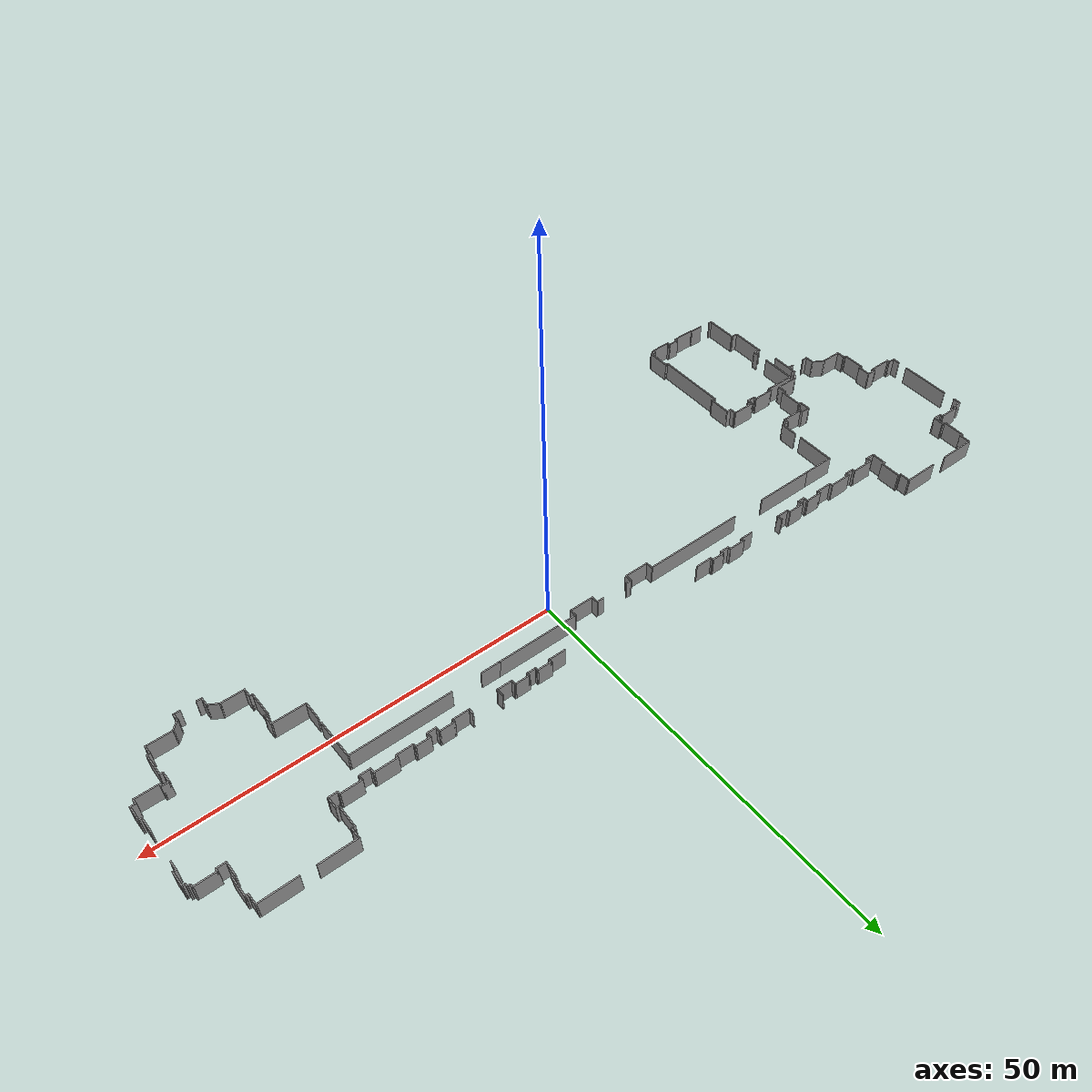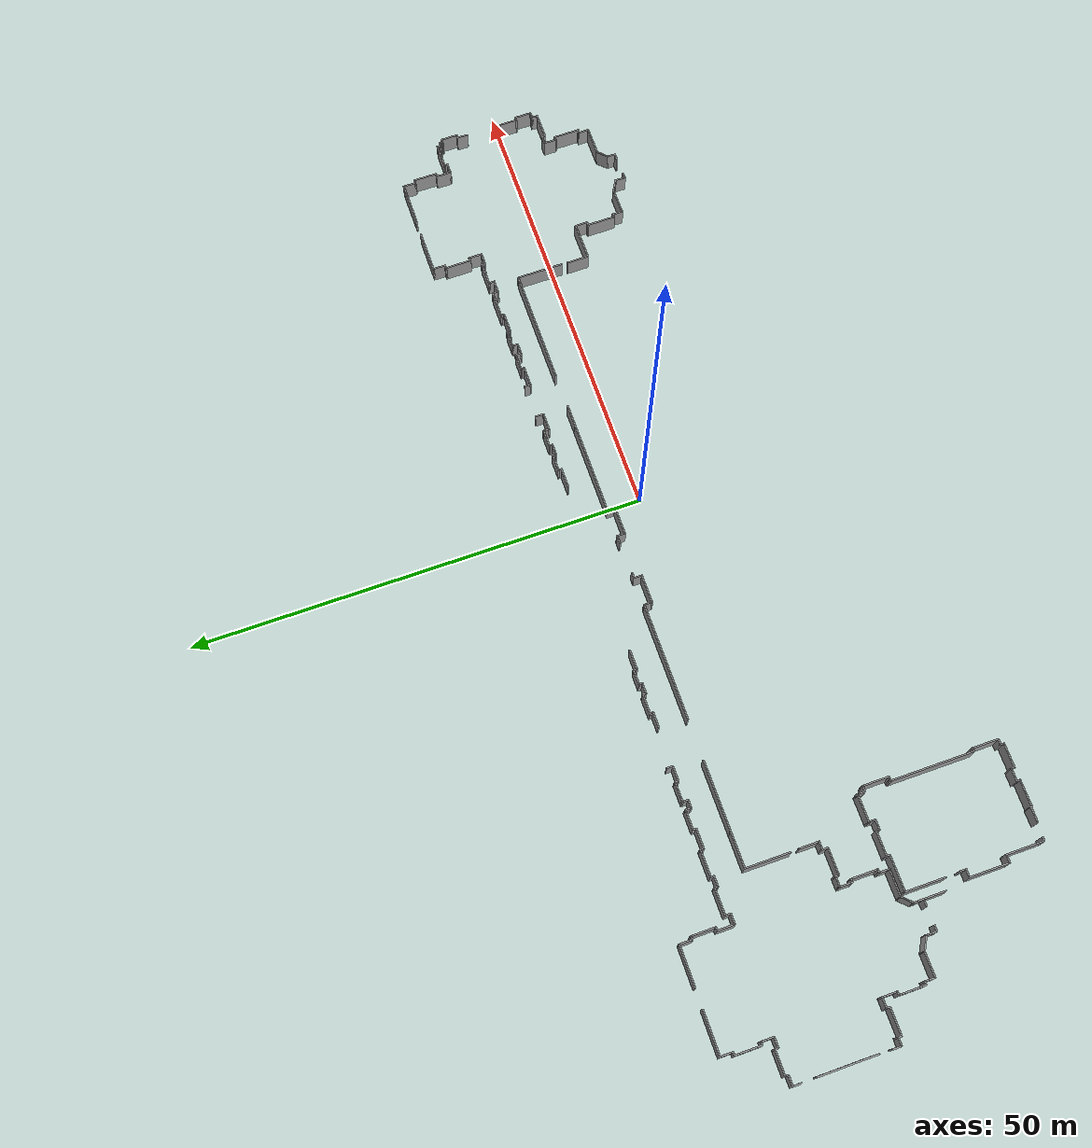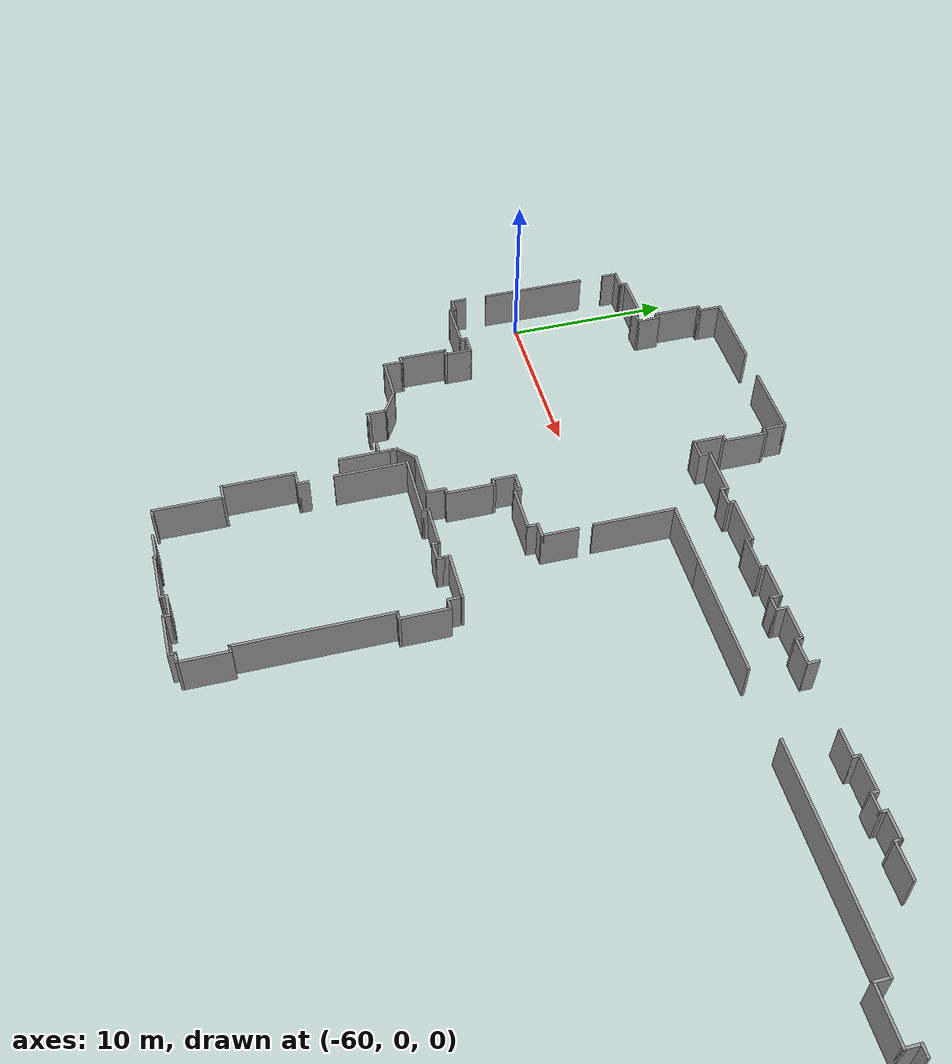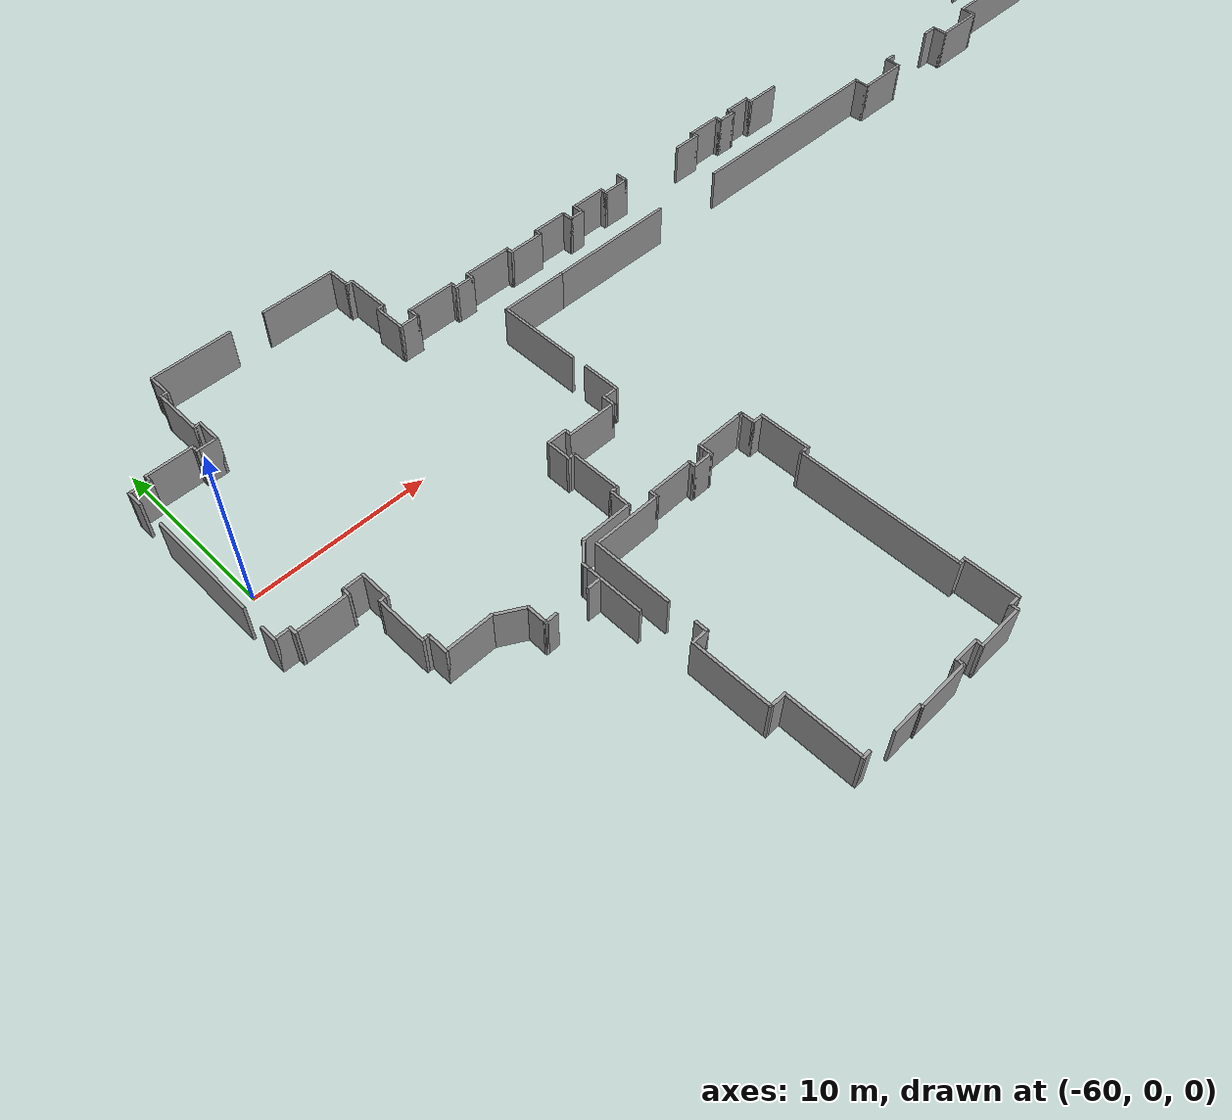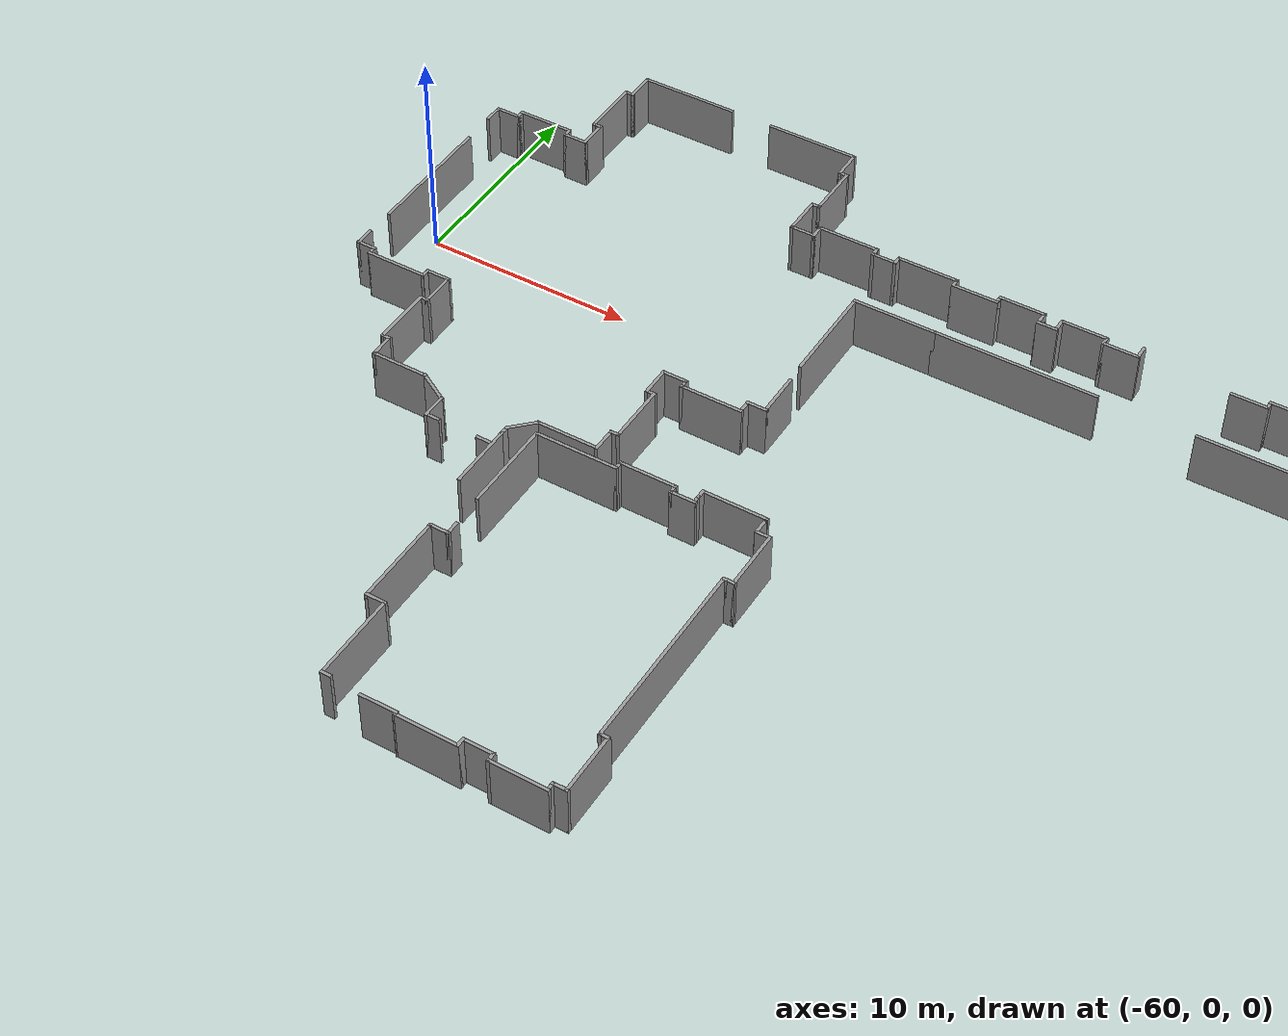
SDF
<?xml version='1.0'?>
<sdf version='1.7'>
  <model name='Building_1'>
    <pose>-6.53713 -6.30976 0 0 -0 0</pose>
    <link name='Wall_0'>
      <collision name='Wall_0_Collision'>
        <geometry>
          <box>
            <size>0.75 0.15 2.5</size>
          </box>
        </geometry>
        <pose>0 0 1.25 0 -0 0</pose>
      </collision>
      <visual name='Wall_0_Visual'>
        <pose>0 0 1.25 0 -0 0</pose>
        <geometry>
          <box>
            <size>0.75 0.15 2.5</size>
          </box>
        </geometry>
        <material>
          <script>
            <uri>file://media/materials/scripts/gazebo.material</uri>
            <name>Gazebo/Grey</name>
          </script>
          <ambient>1 1 1 1</ambient>
        </material>
        <meta>
          <layer>0</layer>
        </meta>
      </visual>
      <pose>-30.9211 -3.55801 0 0 -0 -1.5708</pose>
    </link>
    <link name='Wall_1'>
      <collision name='Wall_1_Collision'>
        <geometry>
          <box>
            <size>0.75 0.15 2.5</size>
          </box>
        </geometry>
        <pose>0 0 1.25 0 -0 0</pose>
      </collision>
      <visual name='Wall_1_Visual'>
        <pose>0 0 1.25 0 -0 0</pose>
        <geometry>
          <box>
            <size>0.75 0.15 2.5</size>
          </box>
        </geometry>
        <material>
          <script>
            <uri>file://media/materials/scripts/gazebo.material</uri>
            <name>Gazebo/Grey</name>
          </script>
          <ambient>1 1 1 1</ambient>
        </material>
        <meta>
          <layer>0</layer>
        </meta>
      </visual>
      <pose>-30.6211 -3.85801 0 0 -0 0</pose>
    </link>
    <link name='Wall_10'>
      <collision name='Wall_10_Collision'>
        <geometry>
          <box>
            <size>2.75 0.15 2.5</size>
          </box>
        </geometry>
        <pose>0 0 1.25 0 -0 0</pose>
      </collision>
      <visual name='Wall_10_Visual'>
        <pose>0 0 1.25 0 -0 0</pose>
        <geometry>
          <box>
            <size>2.75 0.15 2.5</size>
          </box>
        </geometry>
        <material>
          <script>
            <uri>file://media/materials/scripts/gazebo.material</uri>
            <name>Gazebo/Grey</name>
          </script>
          <ambient>1 1 1 1</ambient>
        </material>
        <meta>
          <layer>0</layer>
        </meta>
      </visual>
      <pose>-32.3211 -19.008 0 0 -0 3.14159</pose>
    </link>
    <link name='Wall_100'>
      <collision name='Wall_100_Collision'>
        <geometry>
          <box>
            <size>3 0.15 2.5</size>
          </box>
        </geometry>
        <pose>0 0 1.25 0 -0 0</pose>
      </collision>
      <visual name='Wall_100_Visual'>
        <pose>0 0 1.25 0 -0 0</pose>
        <geometry>
          <box>
            <size>3 0.15 2.5</size>
          </box>
        </geometry>
        <material>
          <script>
            <uri>file://media/materials/scripts/gazebo.material</uri>
            <name>Gazebo/Grey</name>
          </script>
          <ambient>1 1 1 1</ambient>
        </material>
        <meta>
          <layer>0</layer>
        </meta>
      </visual>
      <pose>50.7832 -0.74149 0 0 -0 1.5708</pose>
    </link>
    <link name='Wall_101'>
      <collision name='Wall_101_Collision'>
        <geometry>
          <box>
            <size>0.5 0.15 2.5</size>
          </box>
        </geometry>
        <pose>0 0 1.25 0 -0 0</pose>
      </collision>
      <visual name='Wall_101_Visual'>
        <pose>0 0 1.25 0 -0 0</pose>
        <geometry>
          <box>
            <size>0.5 0.15 2.5</size>
          </box>
        </geometry>
        <material>
          <script>
            <uri>file://media/materials/scripts/gazebo.material</uri>
            <name>Gazebo/Grey</name>
          </script>
          <ambient>1 1 1 1</ambient>
        </material>
        <meta>
          <layer>0</layer>
        </meta>
      </visual>
      <pose>50.6082 0.68351 0 0 -0 3.14159</pose>
    </link>
    <link name='Wall_102'>
      <collision name='Wall_102_Collision'>
        <geometry>
          <box>
            <size>1.5 0.15 2.5</size>
          </box>
        </geometry>
        <pose>0 0 1.25 0 -0 0</pose>
      </collision>
      <visual name='Wall_102_Visual'>
        <pose>0 0 1.25 0 -0 0</pose>
        <geometry>
          <box>
            <size>1.5 0.15 2.5</size>
          </box>
        </geometry>
        <material>
          <script>
            <uri>file://media/materials/scripts/gazebo.material</uri>
            <name>Gazebo/Grey</name>
          </script>
          <ambient>1 1 1 1</ambient>
        </material>
        <meta>
          <layer>0</layer>
        </meta>
      </visual>
      <pose>50.4332 1.35851 0 0 -0 1.5708</pose>
    </link>
    <link name='Wall_103'>
      <collision name='Wall_103_Collision'>
        <geometry>
          <box>
            <size>1 0.15 2.5</size>
          </box>
        </geometry>
        <pose>0 0 1.25 0 -0 0</pose>
      </collision>
      <visual name='Wall_103_Visual'>
        <pose>0 0 1.25 0 -0 0</pose>
        <geometry>
          <box>
            <size>1 0.15 2.5</size>
          </box>
        </geometry>
        <material>
          <script>
            <uri>file://media/materials/scripts/gazebo.material</uri>
            <name>Gazebo/Grey</name>
          </script>
          <ambient>1 1 1 1</ambient>
        </material>
        <meta>
          <layer>0</layer>
        </meta>
      </visual>
      <pose>50.8582 2.03351 0 0 -0 0</pose>
    </link>
    <link name='Wall_104'>
      <collision name='Wall_104_Collision'>
        <geometry>
          <box>
            <size>0.5 0.15 2.5</size>
          </box>
        </geometry>
        <pose>0 0 1.25 0 -0 0</pose>
      </collision>
      <visual name='Wall_104_Visual'>
        <pose>0 0 1.25 0 -0 0</pose>
        <geometry>
          <box>
            <size>0.5 0.15 2.5</size>
          </box>
        </geometry>
        <material>
          <script>
            <uri>file://media/materials/scripts/gazebo.material</uri>
            <name>Gazebo/Grey</name>
          </script>
          <ambient>1 1 1 1</ambient>
        </material>
        <meta>
          <layer>0</layer>
        </meta>
      </visual>
      <pose>51.2832 1.85851 0 0 -0 -1.5708</pose>
    </link>
    <link name='Wall_105'>
      <collision name='Wall_105_Collision'>
        <geometry>
          <box>
            <size>3 0.15 2.5</size>
          </box>
        </geometry>
        <pose>0 0 1.25 0 -0 0</pose>
      </collision>
      <visual name='Wall_105_Visual'>
        <pose>0 0 1.25 0 -0 0</pose>
        <geometry>
          <box>
            <size>3 0.15 2.5</size>
          </box>
        </geometry>
        <material>
          <script>
            <uri>file://media/materials/scripts/gazebo.material</uri>
            <name>Gazebo/Grey</name>
          </script>
          <ambient>1 1 1 1</ambient>
        </material>
        <meta>
          <layer>0</layer>
        </meta>
      </visual>
      <pose>52.7082 1.68351 0 0 -0 0</pose>
    </link>
    <link name='Wall_106'>
      <collision name='Wall_106_Collision'>
        <geometry>
          <box>
            <size>0.75 0.15 2.5</size>
          </box>
        </geometry>
        <pose>0 0 1.25 0 -0 0</pose>
      </collision>
      <visual name='Wall_106_Visual'>
        <pose>0 0 1.25 0 -0 0</pose>
        <geometry>
          <box>
            <size>0.75 0.15 2.5</size>
          </box>
        </geometry>
        <material>
          <script>
            <uri>file://media/materials/scripts/gazebo.material</uri>
            <name>Gazebo/Grey</name>
          </script>
          <ambient>1 1 1 1</ambient>
        </material>
        <meta>
          <layer>0</layer>
        </meta>
      </visual>
      <pose>54.1332 1.98351 0 0 -0 1.5708</pose>
    </link>
    <link name='Wall_107'>
      <collision name='Wall_107_Collision'>
        <geometry>
          <box>
            <size>0.75 0.15 2.5</size>
          </box>
        </geometry>
        <pose>0 0 1.25 0 -0 0</pose>
      </collision>
      <visual name='Wall_107_Visual'>
        <pose>0 0 1.25 0 -0 0</pose>
        <geometry>
          <box>
            <size>0.75 0.15 2.5</size>
          </box>
        </geometry>
        <material>
          <script>
            <uri>file://media/materials/scripts/gazebo.material</uri>
            <name>Gazebo/Grey</name>
          </script>
          <ambient>1 1 1 1</ambient>
        </material>
        <meta>
          <layer>0</layer>
        </meta>
      </visual>
      <pose>54.4332 2.28351 0 0 -0 0</pose>
    </link>
    <link name='Wall_108'>
      <collision name='Wall_108_Collision'>
        <geometry>
          <box>
            <size>2 0.15 2.5</size>
          </box>
        </geometry>
        <pose>0 0 1.25 0 -0 0</pose>
      </collision>
      <visual name='Wall_108_Visual'>
        <pose>0 0 1.25 0 -0 0</pose>
        <geometry>
          <box>
            <size>2 0.15 2.5</size>
          </box>
        </geometry>
        <material>
          <script>
            <uri>file://media/materials/scripts/gazebo.material</uri>
            <name>Gazebo/Grey</name>
          </script>
          <ambient>1 1 1 1</ambient>
        </material>
        <meta>
          <layer>0</layer>
        </meta>
      </visual>
      <pose>54.7332 3.20851 0 0 -0 1.5708</pose>
    </link>
    <link name='Wall_109'>
      <collision name='Wall_109_Collision'>
        <geometry>
          <box>
            <size>0.5 0.15 2.5</size>
          </box>
        </geometry>
        <pose>0 0 1.25 0 -0 0</pose>
      </collision>
      <visual name='Wall_109_Visual'>
        <pose>0 0 1.25 0 -0 0</pose>
        <geometry>
          <box>
            <size>0.5 0.15 2.5</size>
          </box>
        </geometry>
        <material>
          <script>
            <uri>file://media/materials/scripts/gazebo.material</uri>
            <name>Gazebo/Grey</name>
          </script>
          <ambient>1 1 1 1</ambient>
        </material>
        <meta>
          <layer>0</layer>
        </meta>
      </visual>
      <pose>54.5582 4.13351 0 0 -0 3.14159</pose>
    </link>
    <link name='Wall_11'>
      <collision name='Wall_11_Collision'>
        <geometry>
          <box>
            <size>0.5 0.15 2.5</size>
          </box>
        </geometry>
        <pose>0 0 1.25 0 -0 0</pose>
      </collision>
      <visual name='Wall_11_Visual'>
        <pose>0 0 1.25 0 -0 0</pose>
        <geometry>
          <box>
            <size>0.5 0.15 2.5</size>
          </box>
        </geometry>
        <material>
          <script>
            <uri>file://media/materials/scripts/gazebo.material</uri>
            <name>Gazebo/Grey</name>
          </script>
          <ambient>1 1 1 1</ambient>
        </material>
        <meta>
          <layer>0</layer>
        </meta>
      </visual>
      <pose>-33.6211 -18.833 0 0 -0 1.5708</pose>
    </link>
    <link name='Wall_110'>
      <collision name='Wall_110_Collision'>
        <geometry>
          <box>
            <size>2 0.15 2.5</size>
          </box>
        </geometry>
        <pose>0 0 1.25 0 -0 0</pose>
      </collision>
      <visual name='Wall_110_Visual'>
        <pose>0 0 1.25 0 -0 0</pose>
        <geometry>
          <box>
            <size>2 0.15 2.5</size>
          </box>
        </geometry>
        <material>
          <script>
            <uri>file://media/materials/scripts/gazebo.material</uri>
            <name>Gazebo/Grey</name>
          </script>
          <ambient>1 1 1 1</ambient>
        </material>
        <meta>
          <layer>0</layer>
        </meta>
      </visual>
      <pose>54.3832 5.05851 0 0 -0 1.5708</pose>
    </link>
    <link name='Wall_112'>
      <collision name='Wall_112_Collision'>
        <geometry>
          <box>
            <size>1.25 0.15 2.5</size>
          </box>
        </geometry>
        <pose>0 0 1.25 0 -0 0</pose>
      </collision>
      <visual name='Wall_112_Visual'>
        <pose>0 0 1.25 0 -0 0</pose>
        <geometry>
          <box>
            <size>1.25 0.15 2.5</size>
          </box>
        </geometry>
        <material>
          <script>
            <uri>file://media/materials/scripts/gazebo.material</uri>
            <name>Gazebo/Grey</name>
          </script>
          <ambient>1 1 1 1</ambient>
        </material>
        <meta>
          <layer>0</layer>
        </meta>
      </visual>
      <pose>54.3806 10.6744 0 0 -0 1.5708</pose>
    </link>
    <link name='Wall_113'>
      <collision name='Wall_113_Collision'>
        <geometry>
          <box>
            <size>0.5 0.15 2.5</size>
          </box>
        </geometry>
        <pose>0 0 1.25 0 -0 0</pose>
      </collision>
      <visual name='Wall_113_Visual'>
        <pose>0 0 1.25 0 -0 0</pose>
        <geometry>
          <box>
            <size>0.5 0.15 2.5</size>
          </box>
        </geometry>
        <material>
          <script>
            <uri>file://media/materials/scripts/gazebo.material</uri>
            <name>Gazebo/Grey</name>
          </script>
          <ambient>1 1 1 1</ambient>
        </material>
        <meta>
          <layer>0</layer>
        </meta>
      </visual>
      <pose>54.5556 11.2244 0 0 -0 0</pose>
    </link>
    <link name='Wall_114'>
      <collision name='Wall_114_Collision'>
        <geometry>
          <box>
            <size>2 0.15 2.5</size>
          </box>
        </geometry>
        <pose>0 0 1.25 0 -0 0</pose>
      </collision>
      <visual name='Wall_114_Visual'>
        <pose>0 0 1.25 0 -0 0</pose>
        <geometry>
          <box>
            <size>2 0.15 2.5</size>
          </box>
        </geometry>
        <material>
          <script>
            <uri>file://media/materials/scripts/gazebo.material</uri>
            <name>Gazebo/Grey</name>
          </script>
          <ambient>1 1 1 1</ambient>
        </material>
        <meta>
          <layer>0</layer>
        </meta>
      </visual>
      <pose>54.7306 12.1494 0 0 -0 1.5708</pose>
    </link>
    <link name='Wall_115'>
      <collision name='Wall_115_Collision'>
        <geometry>
          <box>
            <size>0.5 0.15 2.5</size>
          </box>
        </geometry>
        <pose>0 0 1.25 0 -0 0</pose>
      </collision>
      <visual name='Wall_115_Visual'>
        <pose>0 0 1.25 0 -0 0</pose>
        <geometry>
          <box>
            <size>0.5 0.15 2.5</size>
          </box>
        </geometry>
        <material>
          <script>
            <uri>file://media/materials/scripts/gazebo.material</uri>
            <name>Gazebo/Grey</name>
          </script>
          <ambient>1 1 1 1</ambient>
        </material>
        <meta>
          <layer>0</layer>
        </meta>
      </visual>
      <pose>54.5556 13.0744 0 0 -0 3.14159</pose>
    </link>
    <link name='Wall_116'>
      <collision name='Wall_116_Collision'>
        <geometry>
          <box>
            <size>0.5 0.15 2.5</size>
          </box>
        </geometry>
        <pose>0 0 1.25 0 -0 0</pose>
      </collision>
      <visual name='Wall_116_Visual'>
        <pose>0 0 1.25 0 -0 0</pose>
        <geometry>
          <box>
            <size>0.5 0.15 2.5</size>
          </box>
        </geometry>
        <material>
          <script>
            <uri>file://media/materials/scripts/gazebo.material</uri>
            <name>Gazebo/Grey</name>
          </script>
          <ambient>1 1 1 1</ambient>
        </material>
        <meta>
          <layer>0</layer>
        </meta>
      </visual>
      <pose>54.3806 13.2494 0 0 -0 1.5708</pose>
    </link>
    <link name='Wall_117'>
      <collision name='Wall_117_Collision'>
        <geometry>
          <box>
            <size>0.5 0.15 2.5</size>
          </box>
        </geometry>
        <pose>0 0 1.25 0 -0 0</pose>
      </collision>
      <visual name='Wall_117_Visual'>
        <pose>0 0 1.25 0 -0 0</pose>
        <geometry>
          <box>
            <size>0.5 0.15 2.5</size>
          </box>
        </geometry>
        <material>
          <script>
            <uri>file://media/materials/scripts/gazebo.material</uri>
            <name>Gazebo/Grey</name>
          </script>
          <ambient>1 1 1 1</ambient>
        </material>
        <meta>
          <layer>0</layer>
        </meta>
      </visual>
      <pose>54.2056 13.4244 0 0 -0 3.14159</pose>
    </link>
    <link name='Wall_118'>
      <collision name='Wall_118_Collision'>
        <geometry>
          <box>
            <size>0.5 0.15 2.5</size>
          </box>
        </geometry>
        <pose>0 0 1.25 0 -0 0</pose>
      </collision>
      <visual name='Wall_118_Visual'>
        <pose>0 0 1.25 0 -0 0</pose>
        <geometry>
          <box>
            <size>0.5 0.15 2.5</size>
          </box>
        </geometry>
        <material>
          <script>
            <uri>file://media/materials/scripts/gazebo.material</uri>
            <name>Gazebo/Grey</name>
          </script>
          <ambient>1 1 1 1</ambient>
        </material>
        <meta>
          <layer>0</layer>
        </meta>
      </visual>
      <pose>54.0306 13.5994 0 0 -0 1.5708</pose>
    </link>
    <link name='Wall_119'>
      <collision name='Wall_119_Collision'>
        <geometry>
          <box>
            <size>2.75 0.15 2.5</size>
          </box>
        </geometry>
        <pose>0 0 1.25 0 -0 0</pose>
      </collision>
      <visual name='Wall_119_Visual'>
        <pose>0 0 1.25 0 -0 0</pose>
        <geometry>
          <box>
            <size>2.75 0.15 2.5</size>
          </box>
        </geometry>
        <material>
          <script>
            <uri>file://media/materials/scripts/gazebo.material</uri>
            <name>Gazebo/Grey</name>
          </script>
          <ambient>1 1 1 1</ambient>
        </material>
        <meta>
          <layer>0</layer>
        </meta>
      </visual>
      <pose>52.7306 13.7744 0 0 -0 3.14159</pose>
    </link>
    <link name='Wall_12'>
      <collision name='Wall_12_Collision'>
        <geometry>
          <box>
            <size>1.5 0.15 2.5</size>
          </box>
        </geometry>
        <pose>0 0 1.25 0 -0 0</pose>
      </collision>
      <visual name='Wall_12_Visual'>
        <pose>0 0 1.25 0 -0 0</pose>
        <geometry>
          <box>
            <size>1.5 0.15 2.5</size>
          </box>
        </geometry>
        <material>
          <script>
            <uri>file://media/materials/scripts/gazebo.material</uri>
            <name>Gazebo/Grey</name>
          </script>
          <ambient>1 1 1 1</ambient>
        </material>
        <meta>
          <layer>0</layer>
        </meta>
      </visual>
      <pose>-34.2961 -18.658 0 0 -0 3.14159</pose>
    </link>
    <link name='Wall_120'>
      <collision name='Wall_120_Collision'>
        <geometry>
          <box>
            <size>0.5 0.15 2.5</size>
          </box>
        </geometry>
        <pose>0 0 1.25 0 -0 0</pose>
      </collision>
      <visual name='Wall_120_Visual'>
        <pose>0 0 1.25 0 -0 0</pose>
        <geometry>
          <box>
            <size>0.5 0.15 2.5</size>
          </box>
        </geometry>
        <material>
          <script>
            <uri>file://media/materials/scripts/gazebo.material</uri>
            <name>Gazebo/Grey</name>
          </script>
          <ambient>1 1 1 1</ambient>
        </material>
        <meta>
          <layer>0</layer>
        </meta>
      </visual>
      <pose>51.4306 13.5994 0 0 -0 -1.5708</pose>
    </link>
    <link name='Wall_121'>
      <collision name='Wall_121_Collision'>
        <geometry>
          <box>
            <size>1.25 0.15 2.5</size>
          </box>
        </geometry>
        <pose>0 0 1.25 0 -0 0</pose>
      </collision>
      <visual name='Wall_121_Visual'>
        <pose>0 0 1.25 0 -0 0</pose>
        <geometry>
          <box>
            <size>1.25 0.15 2.5</size>
          </box>
        </geometry>
        <material>
          <script>
            <uri>file://media/materials/scripts/gazebo.material</uri>
            <name>Gazebo/Grey</name>
          </script>
          <ambient>1 1 1 1</ambient>
        </material>
        <meta>
          <layer>0</layer>
        </meta>
      </visual>
      <pose>50.8806 13.4244 0 0 -0 3.14159</pose>
    </link>
    <link name='Wall_122'>
      <collision name='Wall_122_Collision'>
        <geometry>
          <box>
            <size>1.75 0.15 2.5</size>
          </box>
        </geometry>
        <pose>0 0 1.25 0 -0 0</pose>
      </collision>
      <visual name='Wall_122_Visual'>
        <pose>0 0 1.25 0 -0 0</pose>
        <geometry>
          <box>
            <size>1.75 0.15 2.5</size>
          </box>
        </geometry>
        <material>
          <script>
            <uri>file://media/materials/scripts/gazebo.material</uri>
            <name>Gazebo/Grey</name>
          </script>
          <ambient>1 1 1 1</ambient>
        </material>
        <meta>
          <layer>0</layer>
        </meta>
      </visual>
      <pose>50.3306 14.2244 0 0 -0 1.5708</pose>
    </link>
    <link name='Wall_123'>
      <collision name='Wall_123_Collision'>
        <geometry>
          <box>
            <size>0.5 0.15 2.5</size>
          </box>
        </geometry>
        <pose>0 0 1.25 0 -0 0</pose>
      </collision>
      <visual name='Wall_123_Visual'>
        <pose>0 0 1.25 0 -0 0</pose>
        <geometry>
          <box>
            <size>0.5 0.15 2.5</size>
          </box>
        </geometry>
        <material>
          <script>
            <uri>file://media/materials/scripts/gazebo.material</uri>
            <name>Gazebo/Grey</name>
          </script>
          <ambient>1 1 1 1</ambient>
        </material>
        <meta>
          <layer>0</layer>
        </meta>
      </visual>
      <pose>50.5056 15.0244 0 0 -0 0</pose>
    </link>
    <link name='Wall_124'>
      <collision name='Wall_124_Collision'>
        <geometry>
          <box>
            <size>2.75 0.15 2.5</size>
          </box>
        </geometry>
        <pose>0 0 1.25 0 -0 0</pose>
      </collision>
      <visual name='Wall_124_Visual'>
        <pose>0 0 1.25 0 -0 0</pose>
        <geometry>
          <box>
            <size>2.75 0.15 2.5</size>
          </box>
        </geometry>
        <material>
          <script>
            <uri>file://media/materials/scripts/gazebo.material</uri>
            <name>Gazebo/Grey</name>
          </script>
          <ambient>1 1 1 1</ambient>
        </material>
        <meta>
          <layer>0</layer>
        </meta>
      </visual>
      <pose>50.6806 16.3244 0 0 -0 1.5708</pose>
    </link>
    <link name='Wall_125'>
      <collision name='Wall_125_Collision'>
        <geometry>
          <box>
            <size>0.5 0.15 2.5</size>
          </box>
        </geometry>
        <pose>0 0 1.25 0 -0 0</pose>
      </collision>
      <visual name='Wall_125_Visual'>
        <pose>0 0 1.25 0 -0 0</pose>
        <geometry>
          <box>
            <size>0.5 0.15 2.5</size>
          </box>
        </geometry>
        <material>
          <script>
            <uri>file://media/materials/scripts/gazebo.material</uri>
            <name>Gazebo/Grey</name>
          </script>
          <ambient>1 1 1 1</ambient>
        </material>
        <meta>
          <layer>0</layer>
        </meta>
      </visual>
      <pose>50.5056 17.6244 0 0 -0 3.14159</pose>
    </link>
    <link name='Wall_126'>
      <collision name='Wall_126_Collision'>
        <geometry>
          <box>
            <size>1.5 0.15 2.5</size>
          </box>
        </geometry>
        <pose>0 0 1.25 0 -0 0</pose>
      </collision>
      <visual name='Wall_126_Visual'>
        <pose>0 0 1.25 0 -0 0</pose>
        <geometry>
          <box>
            <size>1.5 0.15 2.5</size>
          </box>
        </geometry>
        <material>
          <script>
            <uri>file://media/materials/scripts/gazebo.material</uri>
            <name>Gazebo/Grey</name>
          </script>
          <ambient>1 1 1 1</ambient>
        </material>
        <meta>
          <layer>0</layer>
        </meta>
      </visual>
      <pose>50.3306 18.2994 0 0 -0 1.5708</pose>
    </link>
    <link name='Wall_127'>
      <collision name='Wall_127_Collision'>
        <geometry>
          <box>
            <size>4.75 0.15 2.5</size>
          </box>
        </geometry>
        <pose>0 0 1.25 0 -0 0</pose>
      </collision>
      <visual name='Wall_127_Visual'>
        <pose>0 0 1.25 0 -0 0</pose>
        <geometry>
          <box>
            <size>4.75 0.15 2.5</size>
          </box>
        </geometry>
        <material>
          <script>
            <uri>file://media/materials/scripts/gazebo.material</uri>
            <name>Gazebo/Grey</name>
          </script>
          <ambient>1 1 1 1</ambient>
        </material>
        <meta>
          <layer>0</layer>
        </meta>
      </visual>
      <pose>48.0306 18.9744 0 0 -0 3.14159</pose>
    </link>
    <link name='Wall_129'>
      <collision name='Wall_129_Collision'>
        <geometry>
          <box>
            <size>4.75 0.15 2.5</size>
          </box>
        </geometry>
        <pose>0 0 1.25 0 -0 0</pose>
      </collision>
      <visual name='Wall_129_Visual'>
        <pose>0 0 1.25 0 -0 0</pose>
        <geometry>
          <box>
            <size>4.75 0.15 2.5</size>
          </box>
        </geometry>
        <material>
          <script>
            <uri>file://media/materials/scripts/gazebo.material</uri>
            <name>Gazebo/Grey</name>
          </script>
          <ambient>1 1 1 1</ambient>
        </material>
        <meta>
          <layer>0</layer>
        </meta>
      </visual>
      <pose>41.5139 19.0249 0 0 -0 3.14159</pose>
    </link>
    <link name='Wall_13'>
      <collision name='Wall_13_Collision'>
        <geometry>
          <box>
            <size>0.5 0.15 2.5</size>
          </box>
        </geometry>
        <pose>0 0 1.25 0 -0 0</pose>
      </collision>
      <visual name='Wall_13_Visual'>
        <pose>0 0 1.25 0 -0 0</pose>
        <geometry>
          <box>
            <size>0.5 0.15 2.5</size>
          </box>
        </geometry>
        <material>
          <script>
            <uri>file://media/materials/scripts/gazebo.material</uri>
            <name>Gazebo/Grey</name>
          </script>
          <ambient>1 1 1 1</ambient>
        </material>
        <meta>
          <layer>0</layer>
        </meta>
      </visual>
      <pose>-34.9711 -18.833 0 0 -0 -1.5708</pose>
    </link>
    <link name='Wall_130'>
      <collision name='Wall_130_Collision'>
        <geometry>
          <box>
            <size>1.5 0.15 2.5</size>
          </box>
        </geometry>
        <pose>0 0 1.25 0 -0 0</pose>
      </collision>
      <visual name='Wall_130_Visual'>
        <pose>0 0 1.25 0 -0 0</pose>
        <geometry>
          <box>
            <size>1.5 0.15 2.5</size>
          </box>
        </geometry>
        <material>
          <script>
            <uri>file://media/materials/scripts/gazebo.material</uri>
            <name>Gazebo/Grey</name>
          </script>
          <ambient>1 1 1 1</ambient>
        </material>
        <meta>
          <layer>0</layer>
        </meta>
      </visual>
      <pose>39.2139 18.3499 0 0 -0 -1.5708</pose>
    </link>
    <link name='Wall_131'>
      <collision name='Wall_131_Collision'>
        <geometry>
          <box>
            <size>0.5 0.15 2.5</size>
          </box>
        </geometry>
        <pose>0 0 1.25 0 -0 0</pose>
      </collision>
      <visual name='Wall_131_Visual'>
        <pose>0 0 1.25 0 -0 0</pose>
        <geometry>
          <box>
            <size>0.5 0.15 2.5</size>
          </box>
        </geometry>
        <material>
          <script>
            <uri>file://media/materials/scripts/gazebo.material</uri>
            <name>Gazebo/Grey</name>
          </script>
          <ambient>1 1 1 1</ambient>
        </material>
        <meta>
          <layer>0</layer>
        </meta>
      </visual>
      <pose>39.0389 17.6749 0 0 -0 3.14159</pose>
    </link>
    <link name='Wall_132'>
      <collision name='Wall_132_Collision'>
        <geometry>
          <box>
            <size>3 0.15 2.5</size>
          </box>
        </geometry>
        <pose>0 0 1.25 0 -0 0</pose>
      </collision>
      <visual name='Wall_132_Visual'>
        <pose>0 0 1.25 0 -0 0</pose>
        <geometry>
          <box>
            <size>3 0.15 2.5</size>
          </box>
        </geometry>
        <material>
          <script>
            <uri>file://media/materials/scripts/gazebo.material</uri>
            <name>Gazebo/Grey</name>
          </script>
          <ambient>1 1 1 1</ambient>
        </material>
        <meta>
          <layer>0</layer>
        </meta>
      </visual>
      <pose>38.8639 16.2499 0 0 -0 -1.5708</pose>
    </link>
    <link name='Wall_135'>
      <collision name='Wall_135_Collision'>
        <geometry>
          <box>
            <size>0.5 0.15 2.5</size>
          </box>
        </geometry>
        <pose>0 0 1.25 0 -0 0</pose>
      </collision>
      <visual name='Wall_135_Visual'>
        <pose>0 0 1.25 0 -0 0</pose>
        <geometry>
          <box>
            <size>0.5 0.15 2.5</size>
          </box>
        </geometry>
        <material>
          <script>
            <uri>file://media/materials/scripts/gazebo.material</uri>
            <name>Gazebo/Grey</name>
          </script>
          <ambient>1 1 1 1</ambient>
        </material>
        <meta>
          <layer>0</layer>
        </meta>
      </visual>
      <pose>39.0389 14.8249 0 0 -0 0</pose>
    </link>
    <link name='Wall_136'>
      <collision name='Wall_136_Collision'>
        <geometry>
          <box>
            <size>1.5 0.15 2.5</size>
          </box>
        </geometry>
        <pose>0 0 1.25 0 -0 0</pose>
      </collision>
      <visual name='Wall_136_Visual'>
        <pose>0 0 1.25 0 -0 0</pose>
        <geometry>
          <box>
            <size>1.5 0.15 2.5</size>
          </box>
        </geometry>
        <material>
          <script>
            <uri>file://media/materials/scripts/gazebo.material</uri>
            <name>Gazebo/Grey</name>
          </script>
          <ambient>1 1 1 1</ambient>
        </material>
        <meta>
          <layer>0</layer>
        </meta>
      </visual>
      <pose>39.2139 14.1499 0 0 -0 -1.5708</pose>
    </link>
    <link name='Wall_137'>
      <collision name='Wall_137_Collision'>
        <geometry>
          <box>
            <size>0.25 0.15 2.5</size>
          </box>
        </geometry>
        <pose>0 0 1.25 0 -0 0</pose>
      </collision>
      <visual name='Wall_137_Visual'>
        <pose>0 0 1.25 0 -0 0</pose>
        <geometry>
          <box>
            <size>0.25 0.15 2.5</size>
          </box>
        </geometry>
        <material>
          <script>
            <uri>file://media/materials/scripts/gazebo.material</uri>
            <name>Gazebo/Grey</name>
          </script>
          <ambient>1 1 1 1</ambient>
        </material>
        <meta>
          <layer>0</layer>
        </meta>
      </visual>
      <pose>39.2139 13.4249 0 0 -0 -1.5708</pose>
    </link>
    <link name='Wall_138'>
      <collision name='Wall_138_Collision'>
        <geometry>
          <box>
            <size>1.25 0.15 2.5</size>
          </box>
        </geometry>
        <pose>0 0 1.25 0 -0 0</pose>
      </collision>
      <visual name='Wall_138_Visual'>
        <pose>0 0 1.25 0 -0 0</pose>
        <geometry>
          <box>
            <size>1.25 0.15 2.5</size>
          </box>
        </geometry>
        <material>
          <script>
            <uri>file://media/materials/scripts/gazebo.material</uri>
            <name>Gazebo/Grey</name>
          </script>
          <ambient>1 1 1 1</ambient>
        </material>
        <meta>
          <layer>0</layer>
        </meta>
      </visual>
      <pose>38.6639 13.3749 0 0 -0 3.14159</pose>
    </link>
    <link name='Wall_139'>
      <collision name='Wall_139_Collision'>
        <geometry>
          <box>
            <size>0.5 0.15 2.5</size>
          </box>
        </geometry>
        <pose>0 0 1.25 0 -0 0</pose>
      </collision>
      <visual name='Wall_139_Visual'>
        <pose>0 0 1.25 0 -0 0</pose>
        <geometry>
          <box>
            <size>0.5 0.15 2.5</size>
          </box>
        </geometry>
        <material>
          <script>
            <uri>file://media/materials/scripts/gazebo.material</uri>
            <name>Gazebo/Grey</name>
          </script>
          <ambient>1 1 1 1</ambient>
        </material>
        <meta>
          <layer>0</layer>
        </meta>
      </visual>
      <pose>38.1139 13.5499 0 0 -0 1.5708</pose>
    </link>
    <link name='Wall_14'>
      <collision name='Wall_14_Collision'>
        <geometry>
          <box>
            <size>3 0.15 2.5</size>
          </box>
        </geometry>
        <pose>0 0 1.25 0 -0 0</pose>
      </collision>
      <visual name='Wall_14_Visual'>
        <pose>0 0 1.25 0 -0 0</pose>
        <geometry>
          <box>
            <size>3 0.15 2.5</size>
          </box>
        </geometry>
        <material>
          <script>
            <uri>file://media/materials/scripts/gazebo.material</uri>
            <name>Gazebo/Grey</name>
          </script>
          <ambient>1 1 1 1</ambient>
        </material>
        <meta>
          <layer>0</layer>
        </meta>
      </visual>
      <pose>-36.3961 -19.008 0 0 -0 3.14159</pose>
    </link>
    <link name='Wall_140'>
      <collision name='Wall_140_Collision'>
        <geometry>
          <box>
            <size>2.75 0.15 2.5</size>
          </box>
        </geometry>
        <pose>0 0 1.25 0 -0 0</pose>
      </collision>
      <visual name='Wall_140_Visual'>
        <pose>0 0 1.25 0 -0 0</pose>
        <geometry>
          <box>
            <size>2.75 0.15 2.5</size>
          </box>
        </geometry>
        <material>
          <script>
            <uri>file://media/materials/scripts/gazebo.material</uri>
            <name>Gazebo/Grey</name>
          </script>
          <ambient>1 1 1 1</ambient>
        </material>
        <meta>
          <layer>0</layer>
        </meta>
      </visual>
      <pose>36.8139 13.7249 0 0 -0 3.14159</pose>
    </link>
    <link name='Wall_141'>
      <collision name='Wall_141_Collision'>
        <geometry>
          <box>
            <size>0.75 0.15 2.5</size>
          </box>
        </geometry>
        <pose>0 0 1.25 0 -0 0</pose>
      </collision>
      <visual name='Wall_141_Visual'>
        <pose>0 0 1.25 0 -0 0</pose>
        <geometry>
          <box>
            <size>0.75 0.15 2.5</size>
          </box>
        </geometry>
        <material>
          <script>
            <uri>file://media/materials/scripts/gazebo.material</uri>
            <name>Gazebo/Grey</name>
          </script>
          <ambient>1 1 1 1</ambient>
        </material>
        <meta>
          <layer>0</layer>
        </meta>
      </visual>
      <pose>35.5139 13.4249 0 0 -0 -1.5708</pose>
    </link>
    <link name='Wall_142'>
      <collision name='Wall_142_Collision'>
        <geometry>
          <box>
            <size>1.5 0.15 2.5</size>
          </box>
        </geometry>
        <pose>0 0 1.25 0 -0 0</pose>
      </collision>
      <visual name='Wall_142_Visual'>
        <pose>0 0 1.25 0 -0 0</pose>
        <geometry>
          <box>
            <size>1.5 0.15 2.5</size>
          </box>
        </geometry>
        <material>
          <script>
            <uri>file://media/materials/scripts/gazebo.material</uri>
            <name>Gazebo/Grey</name>
          </script>
          <ambient>1 1 1 1</ambient>
        </material>
        <meta>
          <layer>0</layer>
        </meta>
      </visual>
      <pose>34.8389 13.1249 0 0 -0 3.14159</pose>
    </link>
    <link name='Wall_143'>
      <collision name='Wall_143_Collision'>
        <geometry>
          <box>
            <size>0.75 0.15 2.5</size>
          </box>
        </geometry>
        <pose>0 0 1.25 0 -0 0</pose>
      </collision>
      <visual name='Wall_143_Visual'>
        <pose>0 0 1.25 0 -0 0</pose>
        <geometry>
          <box>
            <size>0.75 0.15 2.5</size>
          </box>
        </geometry>
        <material>
          <script>
            <uri>file://media/materials/scripts/gazebo.material</uri>
            <name>Gazebo/Grey</name>
          </script>
          <ambient>1 1 1 1</ambient>
        </material>
        <meta>
          <layer>0</layer>
        </meta>
      </visual>
      <pose>34.1639 13.4249 0 0 -0 1.5708</pose>
    </link>
    <link name='Wall_144'>
      <collision name='Wall_144_Collision'>
        <geometry>
          <box>
            <size>3 0.15 2.5</size>
          </box>
        </geometry>
        <pose>0 0 1.25 0 -0 0</pose>
      </collision>
      <visual name='Wall_144_Visual'>
        <pose>0 0 1.25 0 -0 0</pose>
        <geometry>
          <box>
            <size>3 0.15 2.5</size>
          </box>
        </geometry>
        <material>
          <script>
            <uri>file://media/materials/scripts/gazebo.material</uri>
            <name>Gazebo/Grey</name>
          </script>
          <ambient>1 1 1 1</ambient>
        </material>
        <meta>
          <layer>0</layer>
        </meta>
      </visual>
      <pose>32.7389 13.7249 0 0 -0 3.14159</pose>
    </link>
    <link name='Wall_145'>
      <collision name='Wall_145_Collision'>
        <geometry>
          <box>
            <size>0.5 0.15 2.5</size>
          </box>
        </geometry>
        <pose>0 0 1.25 0 -0 0</pose>
      </collision>
      <visual name='Wall_145_Visual'>
        <pose>0 0 1.25 0 -0 0</pose>
        <geometry>
          <box>
            <size>0.5 0.15 2.5</size>
          </box>
        </geometry>
        <material>
          <script>
            <uri>file://media/materials/scripts/gazebo.material</uri>
            <name>Gazebo/Grey</name>
          </script>
          <ambient>1 1 1 1</ambient>
        </material>
        <meta>
          <layer>0</layer>
        </meta>
      </visual>
      <pose>31.3139 13.5499 0 0 -0 -1.5708</pose>
    </link>
    <link name='Wall_146'>
      <collision name='Wall_146_Collision'>
        <geometry>
          <box>
            <size>2.25 0.15 2.5</size>
          </box>
        </geometry>
        <pose>0 0 1.25 0 -0 0</pose>
      </collision>
      <visual name='Wall_146_Visual'>
        <pose>0 0 1.25 0 -0 0</pose>
        <geometry>
          <box>
            <size>2.25 0.15 2.5</size>
          </box>
        </geometry>
        <material>
          <script>
            <uri>file://media/materials/scripts/gazebo.material</uri>
            <name>Gazebo/Grey</name>
          </script>
          <ambient>1 1 1 1</ambient>
        </material>
        <meta>
          <layer>0</layer>
        </meta>
      </visual>
      <pose>30.2639 13.3749 0 0 -0 3.14159</pose>
    </link>
    <link name='Wall_147'>
      <collision name='Wall_147_Collision'>
        <geometry>
          <box>
            <size>0.5 0.15 2.5</size>
          </box>
        </geometry>
        <pose>0 0 1.25 0 -0 0</pose>
      </collision>
      <visual name='Wall_147_Visual'>
        <pose>0 0 1.25 0 -0 0</pose>
        <geometry>
          <box>
            <size>0.5 0.15 2.5</size>
          </box>
        </geometry>
        <material>
          <script>
            <uri>file://media/materials/scripts/gazebo.material</uri>
            <name>Gazebo/Grey</name>
          </script>
          <ambient>1 1 1 1</ambient>
        </material>
        <meta>
          <layer>0</layer>
        </meta>
      </visual>
      <pose>29.2139 13.5499 0 0 -0 1.5708</pose>
    </link>
    <link name='Wall_148'>
      <collision name='Wall_148_Collision'>
        <geometry>
          <box>
            <size>2 0.15 2.5</size>
          </box>
        </geometry>
        <pose>0 0 1.25 0 -0 0</pose>
      </collision>
      <visual name='Wall_148_Visual'>
        <pose>0 0 1.25 0 -0 0</pose>
        <geometry>
          <box>
            <size>2 0.15 2.5</size>
          </box>
        </geometry>
        <material>
          <script>
            <uri>file://media/materials/scripts/gazebo.material</uri>
            <name>Gazebo/Grey</name>
          </script>
          <ambient>1 1 1 1</ambient>
        </material>
        <meta>
          <layer>0</layer>
        </meta>
      </visual>
      <pose>28.2889 13.7249 0 0 -0 3.14159</pose>
    </link>
    <link name='Wall_149'>
      <collision name='Wall_149_Collision'>
        <geometry>
          <box>
            <size>0.75 0.15 2.5</size>
          </box>
        </geometry>
        <pose>0 0 1.25 0 -0 0</pose>
      </collision>
      <visual name='Wall_149_Visual'>
        <pose>0 0 1.25 0 -0 0</pose>
        <geometry>
          <box>
            <size>0.75 0.15 2.5</size>
          </box>
        </geometry>
        <material>
          <script>
            <uri>file://media/materials/scripts/gazebo.material</uri>
            <name>Gazebo/Grey</name>
          </script>
          <ambient>1 1 1 1</ambient>
        </material>
        <meta>
          <layer>0</layer>
        </meta>
      </visual>
      <pose>27.3639 13.4249 0 0 -0 -1.5708</pose>
    </link>
    <link name='Wall_15'>
      <collision name='Wall_15_Collision'>
        <geometry>
          <box>
            <size>0.25 0.15 2.5</size>
          </box>
        </geometry>
        <pose>0 0 1.25 0 -0 0</pose>
      </collision>
      <visual name='Wall_15_Visual'>
        <pose>0 0 1.25 0 -0 0</pose>
        <geometry>
          <box>
            <size>0.25 0.15 2.5</size>
          </box>
        </geometry>
        <material>
          <script>
            <uri>file://media/materials/scripts/gazebo.material</uri>
            <name>Gazebo/Grey</name>
          </script>
          <ambient>1 1 1 1</ambient>
        </material>
        <meta>
          <layer>0</layer>
        </meta>
      </visual>
      <pose>-37.8341 -18.9597 0 0 -0 1.8326</pose>
    </link>
    <link name='Wall_150'>
      <collision name='Wall_150_Collision'>
        <geometry>
          <box>
            <size>1.25 0.15 2.5</size>
          </box>
        </geometry>
        <pose>0 0 1.25 0 -0 0</pose>
      </collision>
      <visual name='Wall_150_Visual'>
        <pose>0 0 1.25 0 -0 0</pose>
        <geometry>
          <box>
            <size>1.25 0.15 2.5</size>
          </box>
        </geometry>
        <material>
          <script>
            <uri>file://media/materials/scripts/gazebo.material</uri>
            <name>Gazebo/Grey</name>
          </script>
          <ambient>1 1 1 1</ambient>
        </material>
        <meta>
          <layer>0</layer>
        </meta>
      </visual>
      <pose>26.8139 13.1249 0 0 -0 3.14159</pose>
    </link>
    <link name='Wall_151'>
      <collision name='Wall_151_Collision'>
        <geometry>
          <box>
            <size>0.75 0.15 2.5</size>
          </box>
        </geometry>
        <pose>0 0 1.25 0 -0 0</pose>
      </collision>
      <visual name='Wall_151_Visual'>
        <pose>0 0 1.25 0 -0 0</pose>
        <geometry>
          <box>
            <size>0.75 0.15 2.5</size>
          </box>
        </geometry>
        <material>
          <script>
            <uri>file://media/materials/scripts/gazebo.material</uri>
            <name>Gazebo/Grey</name>
          </script>
          <ambient>1 1 1 1</ambient>
        </material>
        <meta>
          <layer>0</layer>
        </meta>
      </visual>
      <pose>26.2639 13.4249 0 0 -0 1.5708</pose>
    </link>
    <link name='Wall_152'>
      <collision name='Wall_152_Collision'>
        <geometry>
          <box>
            <size>2 0.15 2.5</size>
          </box>
        </geometry>
        <pose>0 0 1.25 0 -0 0</pose>
      </collision>
      <visual name='Wall_152_Visual'>
        <pose>0 0 1.25 0 -0 0</pose>
        <geometry>
          <box>
            <size>2 0.15 2.5</size>
          </box>
        </geometry>
        <material>
          <script>
            <uri>file://media/materials/scripts/gazebo.material</uri>
            <name>Gazebo/Grey</name>
          </script>
          <ambient>1 1 1 1</ambient>
        </material>
        <meta>
          <layer>0</layer>
        </meta>
      </visual>
      <pose>25.3389 13.7249 0 0 -0 3.14159</pose>
    </link>
    <link name='Wall_153'>
      <collision name='Wall_153_Collision'>
        <geometry>
          <box>
            <size>0.5 0.15 2.5</size>
          </box>
        </geometry>
        <pose>0 0 1.25 0 -0 0</pose>
      </collision>
      <visual name='Wall_153_Visual'>
        <pose>0 0 1.25 0 -0 0</pose>
        <geometry>
          <box>
            <size>0.5 0.15 2.5</size>
          </box>
        </geometry>
        <material>
          <script>
            <uri>file://media/materials/scripts/gazebo.material</uri>
            <name>Gazebo/Grey</name>
          </script>
          <ambient>1 1 1 1</ambient>
        </material>
        <meta>
          <layer>0</layer>
        </meta>
      </visual>
      <pose>24.4139 13.5499 0 0 -0 -1.5708</pose>
    </link>
    <link name='Wall_154'>
      <collision name='Wall_154_Collision'>
        <geometry>
          <box>
            <size>2.25 0.15 2.5</size>
          </box>
        </geometry>
        <pose>0 0 1.25 0 -0 0</pose>
      </collision>
      <visual name='Wall_154_Visual'>
        <pose>0 0 1.25 0 -0 0</pose>
        <geometry>
          <box>
            <size>2.25 0.15 2.5</size>
          </box>
        </geometry>
        <material>
          <script>
            <uri>file://media/materials/scripts/gazebo.material</uri>
            <name>Gazebo/Grey</name>
          </script>
          <ambient>1 1 1 1</ambient>
        </material>
        <meta>
          <layer>0</layer>
        </meta>
      </visual>
      <pose>23.3639 13.3749 0 0 -0 3.14159</pose>
    </link>
    <link name='Wall_155'>
      <collision name='Wall_155_Collision'>
        <geometry>
          <box>
            <size>0.75 0.15 2.5</size>
          </box>
        </geometry>
        <pose>0 0 1.25 0 -0 0</pose>
      </collision>
      <visual name='Wall_155_Visual'>
        <pose>0 0 1.25 0 -0 0</pose>
        <geometry>
          <box>
            <size>0.75 0.15 2.5</size>
          </box>
        </geometry>
        <material>
          <script>
            <uri>file://media/materials/scripts/gazebo.material</uri>
            <name>Gazebo/Grey</name>
          </script>
          <ambient>1 1 1 1</ambient>
        </material>
        <meta>
          <layer>0</layer>
        </meta>
      </visual>
      <pose>22.3139 13.6749 0 0 -0 1.5708</pose>
    </link>
    <link name='Wall_157'>
      <collision name='Wall_157_Collision'>
        <geometry>
          <box>
            <size>1 0.15 2.5</size>
          </box>
        </geometry>
        <pose>0 0 1.25 0 -0 0</pose>
      </collision>
      <visual name='Wall_157_Visual'>
        <pose>0 0 1.25 0 -0 0</pose>
        <geometry>
          <box>
            <size>1 0.15 2.5</size>
          </box>
        </geometry>
        <material>
          <script>
            <uri>file://media/materials/scripts/gazebo.material</uri>
            <name>Gazebo/Grey</name>
          </script>
          <ambient>1 1 1 1</ambient>
        </material>
        <meta>
          <layer>0</layer>
        </meta>
      </visual>
      <pose>18.5409 13.6008 0 0 -0 -1.5708</pose>
    </link>
    <link name='Wall_158'>
      <collision name='Wall_158_Collision'>
        <geometry>
          <box>
            <size>2 0.15 2.5</size>
          </box>
        </geometry>
        <pose>0 0 1.25 0 -0 0</pose>
      </collision>
      <visual name='Wall_158_Visual'>
        <pose>0 0 1.25 0 -0 0</pose>
        <geometry>
          <box>
            <size>2 0.15 2.5</size>
          </box>
        </geometry>
        <material>
          <script>
            <uri>file://media/materials/scripts/gazebo.material</uri>
            <name>Gazebo/Grey</name>
          </script>
          <ambient>1 1 1 1</ambient>
        </material>
        <meta>
          <layer>0</layer>
        </meta>
      </visual>
      <pose>17.6159 13.1758 0 0 -0 3.14159</pose>
    </link>
    <link name='Wall_159'>
      <collision name='Wall_159_Collision'>
        <geometry>
          <box>
            <size>0.75 0.15 2.5</size>
          </box>
        </geometry>
        <pose>0 0 1.25 0 -0 0</pose>
      </collision>
      <visual name='Wall_159_Visual'>
        <pose>0 0 1.25 0 -0 0</pose>
        <geometry>
          <box>
            <size>0.75 0.15 2.5</size>
          </box>
        </geometry>
        <material>
          <script>
            <uri>file://media/materials/scripts/gazebo.material</uri>
            <name>Gazebo/Grey</name>
          </script>
          <ambient>1 1 1 1</ambient>
        </material>
        <meta>
          <layer>0</layer>
        </meta>
      </visual>
      <pose>16.6909 13.4758 0 0 -0 1.5708</pose>
    </link>
    <link name='Wall_16'>
      <collision name='Wall_16_Collision'>
        <geometry>
          <box>
            <size>1.75 0.15 2.5</size>
          </box>
        </geometry>
        <pose>0 0 1.25 0 -0 0</pose>
      </collision>
      <visual name='Wall_16_Visual'>
        <pose>0 0 1.25 0 -0 0</pose>
        <geometry>
          <box>
            <size>1.75 0.15 2.5</size>
          </box>
        </geometry>
        <material>
          <script>
            <uri>file://media/materials/scripts/gazebo.material</uri>
            <name>Gazebo/Grey</name>
          </script>
          <ambient>1 1 1 1</ambient>
        </material>
        <meta>
          <layer>0</layer>
        </meta>
      </visual>
      <pose>-38.647 -18.9114 0 0 -0 3.14159</pose>
    </link>
    <link name='Wall_160'>
      <collision name='Wall_160_Collision'>
        <geometry>
          <box>
            <size>2 0.15 2.5</size>
          </box>
        </geometry>
        <pose>0 0 1.25 0 -0 0</pose>
      </collision>
      <visual name='Wall_160_Visual'>
        <pose>0 0 1.25 0 -0 0</pose>
        <geometry>
          <box>
            <size>2 0.15 2.5</size>
          </box>
        </geometry>
        <material>
          <script>
            <uri>file://media/materials/scripts/gazebo.material</uri>
            <name>Gazebo/Grey</name>
          </script>
          <ambient>1 1 1 1</ambient>
        </material>
        <meta>
          <layer>0</layer>
        </meta>
      </visual>
      <pose>15.7659 13.7758 0 0 -0 3.14159</pose>
    </link>
    <link name='Wall_161'>
      <collision name='Wall_161_Collision'>
        <geometry>
          <box>
            <size>0.5 0.15 2.5</size>
          </box>
        </geometry>
        <pose>0 0 1.25 0 -0 0</pose>
      </collision>
      <visual name='Wall_161_Visual'>
        <pose>0 0 1.25 0 -0 0</pose>
        <geometry>
          <box>
            <size>0.5 0.15 2.5</size>
          </box>
        </geometry>
        <material>
          <script>
            <uri>file://media/materials/scripts/gazebo.material</uri>
            <name>Gazebo/Grey</name>
          </script>
          <ambient>1 1 1 1</ambient>
        </material>
        <meta>
          <layer>0</layer>
        </meta>
      </visual>
      <pose>14.8409 13.6008 0 0 -0 -1.5708</pose>
    </link>
    <link name='Wall_162'>
      <collision name='Wall_162_Collision'>
        <geometry>
          <box>
            <size>1.25 0.15 2.5</size>
          </box>
        </geometry>
        <pose>0 0 1.25 0 -0 0</pose>
      </collision>
      <visual name='Wall_162_Visual'>
        <pose>0 0 1.25 0 -0 0</pose>
        <geometry>
          <box>
            <size>1.25 0.15 2.5</size>
          </box>
        </geometry>
        <material>
          <script>
            <uri>file://media/materials/scripts/gazebo.material</uri>
            <name>Gazebo/Grey</name>
          </script>
          <ambient>1 1 1 1</ambient>
        </material>
        <meta>
          <layer>0</layer>
        </meta>
      </visual>
      <pose>14.2909 13.4258 0 0 -0 3.14159</pose>
    </link>
    <link name='Wall_163'>
      <collision name='Wall_163_Collision'>
        <geometry>
          <box>
            <size>0.5 0.15 2.5</size>
          </box>
        </geometry>
        <pose>0 0 1.25 0 -0 0</pose>
      </collision>
      <visual name='Wall_163_Visual'>
        <pose>0 0 1.25 0 -0 0</pose>
        <geometry>
          <box>
            <size>0.5 0.15 2.5</size>
          </box>
        </geometry>
        <material>
          <script>
            <uri>file://media/materials/scripts/gazebo.material</uri>
            <name>Gazebo/Grey</name>
          </script>
          <ambient>1 1 1 1</ambient>
        </material>
        <meta>
          <layer>0</layer>
        </meta>
      </visual>
      <pose>13.7409 13.6008 0 0 -0 1.5708</pose>
    </link>
    <link name='Wall_164'>
      <collision name='Wall_164_Collision'>
        <geometry>
          <box>
            <size>2 0.15 2.5</size>
          </box>
        </geometry>
        <pose>0 0 1.25 0 -0 0</pose>
      </collision>
      <visual name='Wall_164_Visual'>
        <pose>0 0 1.25 0 -0 0</pose>
        <geometry>
          <box>
            <size>2 0.15 2.5</size>
          </box>
        </geometry>
        <material>
          <script>
            <uri>file://media/materials/scripts/gazebo.material</uri>
            <name>Gazebo/Grey</name>
          </script>
          <ambient>1 1 1 1</ambient>
        </material>
        <meta>
          <layer>0</layer>
        </meta>
      </visual>
      <pose>12.8159 13.7758 0 0 -0 3.14159</pose>
    </link>
    <link name='Wall_165'>
      <collision name='Wall_165_Collision'>
        <geometry>
          <box>
            <size>0.5 0.15 2.5</size>
          </box>
        </geometry>
        <pose>0 0 1.25 0 -0 0</pose>
      </collision>
      <visual name='Wall_165_Visual'>
        <pose>0 0 1.25 0 -0 0</pose>
        <geometry>
          <box>
            <size>0.5 0.15 2.5</size>
          </box>
        </geometry>
        <material>
          <script>
            <uri>file://media/materials/scripts/gazebo.material</uri>
            <name>Gazebo/Grey</name>
          </script>
          <ambient>1 1 1 1</ambient>
        </material>
        <meta>
          <layer>0</layer>
        </meta>
      </visual>
      <pose>11.8909 13.6008 0 0 -0 -1.5708</pose>
    </link>
    <link name='Wall_166'>
      <collision name='Wall_166_Collision'>
        <geometry>
          <box>
            <size>2.25 0.15 2.5</size>
          </box>
        </geometry>
        <pose>0 0 1.25 0 -0 0</pose>
      </collision>
      <visual name='Wall_166_Visual'>
        <pose>0 0 1.25 0 -0 0</pose>
        <geometry>
          <box>
            <size>2.25 0.15 2.5</size>
          </box>
        </geometry>
        <material>
          <script>
            <uri>file://media/materials/scripts/gazebo.material</uri>
            <name>Gazebo/Grey</name>
          </script>
          <ambient>1 1 1 1</ambient>
        </material>
        <meta>
          <layer>0</layer>
        </meta>
      </visual>
      <pose>10.8409 13.4258 0 0 -0 3.14159</pose>
    </link>
    <link name='Wall_18'>
      <collision name='Wall_18_Collision'>
        <geometry>
          <box>
            <size>0.5 0.15 2.5</size>
          </box>
        </geometry>
        <pose>0 0 1.25 0 -0 0</pose>
      </collision>
      <visual name='Wall_18_Visual'>
        <pose>0 0 1.25 0 -0 0</pose>
        <geometry>
          <box>
            <size>0.5 0.15 2.5</size>
          </box>
        </geometry>
        <material>
          <script>
            <uri>file://media/materials/scripts/gazebo.material</uri>
            <name>Gazebo/Grey</name>
          </script>
          <ambient>1 1 1 1</ambient>
        </material>
        <meta>
          <layer>0</layer>
        </meta>
      </visual>
      <pose>-41.1811 -18.7555 0 0 -0 3.14159</pose>
    </link>
    <link name='Wall_183'>
      <collision name='Wall_183_Collision'>
        <geometry>
          <box>
            <size>2.25 0.15 2.5</size>
          </box>
        </geometry>
        <pose>0 0 1.25 0 -0 0</pose>
      </collision>
      <visual name='Wall_183_Visual'>
        <pose>0 0 1.25 0 -0 0</pose>
        <geometry>
          <box>
            <size>2.25 0.15 2.5</size>
          </box>
        </geometry>
        <material>
          <script>
            <uri>file://media/materials/scripts/gazebo.material</uri>
            <name>Gazebo/Grey</name>
          </script>
          <ambient>1 1 1 1</ambient>
        </material>
        <meta>
          <layer>0</layer>
        </meta>
      </visual>
      <pose>-10.4472 13.3899 0 0 -0 3.14159</pose>
    </link>
    <link name='Wall_184'>
      <collision name='Wall_184_Collision'>
        <geometry>
          <box>
            <size>0.5 0.15 2.5</size>
          </box>
        </geometry>
        <pose>0 0 1.25 0 -0 0</pose>
      </collision>
      <visual name='Wall_184_Visual'>
        <pose>0 0 1.25 0 -0 0</pose>
        <geometry>
          <box>
            <size>0.5 0.15 2.5</size>
          </box>
        </geometry>
        <material>
          <script>
            <uri>file://media/materials/scripts/gazebo.material</uri>
            <name>Gazebo/Grey</name>
          </script>
          <ambient>1 1 1 1</ambient>
        </material>
        <meta>
          <layer>0</layer>
        </meta>
      </visual>
      <pose>-11.4972 13.5649 0 0 -0 1.5708</pose>
    </link>
    <link name='Wall_185'>
      <collision name='Wall_185_Collision'>
        <geometry>
          <box>
            <size>1.75 0.15 2.5</size>
          </box>
        </geometry>
        <pose>0 0 1.25 0 -0 0</pose>
      </collision>
      <visual name='Wall_185_Visual'>
        <pose>0 0 1.25 0 -0 0</pose>
        <geometry>
          <box>
            <size>1.75 0.15 2.5</size>
          </box>
        </geometry>
        <material>
          <script>
            <uri>file://media/materials/scripts/gazebo.material</uri>
            <name>Gazebo/Grey</name>
          </script>
          <ambient>1 1 1 1</ambient>
        </material>
        <meta>
          <layer>0</layer>
        </meta>
      </visual>
      <pose>-12.2972 13.7399 0 0 -0 3.14159</pose>
    </link>
    <link name='Wall_186'>
      <collision name='Wall_186_Collision'>
        <geometry>
          <box>
            <size>0.5 0.15 2.5</size>
          </box>
        </geometry>
        <pose>0 0 1.25 0 -0 0</pose>
      </collision>
      <visual name='Wall_186_Visual'>
        <pose>0 0 1.25 0 -0 0</pose>
        <geometry>
          <box>
            <size>0.5 0.15 2.5</size>
          </box>
        </geometry>
        <material>
          <script>
            <uri>file://media/materials/scripts/gazebo.material</uri>
            <name>Gazebo/Grey</name>
          </script>
          <ambient>1 1 1 1</ambient>
        </material>
        <meta>
          <layer>0</layer>
        </meta>
      </visual>
      <pose>-13.0972 13.5649 0 0 -0 -1.5708</pose>
    </link>
    <link name='Wall_187'>
      <collision name='Wall_187_Collision'>
        <geometry>
          <box>
            <size>1.25 0.15 2.5</size>
          </box>
        </geometry>
        <pose>0 0 1.25 0 -0 0</pose>
      </collision>
      <visual name='Wall_187_Visual'>
        <pose>0 0 1.25 0 -0 0</pose>
        <geometry>
          <box>
            <size>1.25 0.15 2.5</size>
          </box>
        </geometry>
        <material>
          <script>
            <uri>file://media/materials/scripts/gazebo.material</uri>
            <name>Gazebo/Grey</name>
          </script>
          <ambient>1 1 1 1</ambient>
        </material>
        <meta>
          <layer>0</layer>
        </meta>
      </visual>
      <pose>-13.6472 13.3899 0 0 -0 3.14159</pose>
    </link>
    <link name='Wall_188'>
      <collision name='Wall_188_Collision'>
        <geometry>
          <box>
            <size>0.5 0.15 2.5</size>
          </box>
        </geometry>
        <pose>0 0 1.25 0 -0 0</pose>
      </collision>
      <visual name='Wall_188_Visual'>
        <pose>0 0 1.25 0 -0 0</pose>
        <geometry>
          <box>
            <size>0.5 0.15 2.5</size>
          </box>
        </geometry>
        <material>
          <script>
            <uri>file://media/materials/scripts/gazebo.material</uri>
            <name>Gazebo/Grey</name>
          </script>
          <ambient>1 1 1 1</ambient>
        </material>
        <meta>
          <layer>0</layer>
        </meta>
      </visual>
      <pose>-14.1972 13.5649 0 0 -0 1.5708</pose>
    </link>
    <link name='Wall_189'>
      <collision name='Wall_189_Collision'>
        <geometry>
          <box>
            <size>2.25 0.15 2.5</size>
          </box>
        </geometry>
        <pose>0 0 1.25 0 -0 0</pose>
      </collision>
      <visual name='Wall_189_Visual'>
        <pose>0 0 1.25 0 -0 0</pose>
        <geometry>
          <box>
            <size>2.25 0.15 2.5</size>
          </box>
        </geometry>
        <material>
          <script>
            <uri>file://media/materials/scripts/gazebo.material</uri>
            <name>Gazebo/Grey</name>
          </script>
          <ambient>1 1 1 1</ambient>
        </material>
        <meta>
          <layer>0</layer>
        </meta>
      </visual>
      <pose>-15.2472 13.7399 0 0 -0 3.14159</pose>
    </link>
    <link name='Wall_19'>
      <collision name='Wall_19_Collision'>
        <geometry>
          <box>
            <size>4.25 0.15 2.5</size>
          </box>
        </geometry>
        <pose>0 0 1.25 0 -0 0</pose>
      </collision>
      <visual name='Wall_19_Visual'>
        <pose>0 0 1.25 0 -0 0</pose>
        <geometry>
          <box>
            <size>4.25 0.15 2.5</size>
          </box>
        </geometry>
        <material>
          <script>
            <uri>file://media/materials/scripts/gazebo.material</uri>
            <name>Gazebo/Grey</name>
          </script>
          <ambient>1 1 1 1</ambient>
        </material>
        <meta>
          <layer>0</layer>
        </meta>
      </visual>
      <pose>-41.3561 -16.7055 0 0 -0 1.5708</pose>
    </link>
    <link name='Wall_190'>
      <collision name='Wall_190_Collision'>
        <geometry>
          <box>
            <size>0.5 0.15 2.5</size>
          </box>
        </geometry>
        <pose>0 0 1.25 0 -0 0</pose>
      </collision>
      <visual name='Wall_190_Visual'>
        <pose>0 0 1.25 0 -0 0</pose>
        <geometry>
          <box>
            <size>0.5 0.15 2.5</size>
          </box>
        </geometry>
        <material>
          <script>
            <uri>file://media/materials/scripts/gazebo.material</uri>
            <name>Gazebo/Grey</name>
          </script>
          <ambient>1 1 1 1</ambient>
        </material>
        <meta>
          <layer>0</layer>
        </meta>
      </visual>
      <pose>-16.2972 13.5649 0 0 -0 -1.5708</pose>
    </link>
    <link name='Wall_191'>
      <collision name='Wall_191_Collision'>
        <geometry>
          <box>
            <size>1.75 0.15 2.5</size>
          </box>
        </geometry>
        <pose>0 0 1.25 0 -0 0</pose>
      </collision>
      <visual name='Wall_191_Visual'>
        <pose>0 0 1.25 0 -0 0</pose>
        <geometry>
          <box>
            <size>1.75 0.15 2.5</size>
          </box>
        </geometry>
        <material>
          <script>
            <uri>file://media/materials/scripts/gazebo.material</uri>
            <name>Gazebo/Grey</name>
          </script>
          <ambient>1 1 1 1</ambient>
        </material>
        <meta>
          <layer>0</layer>
        </meta>
      </visual>
      <pose>-17.0972 13.3899 0 0 -0 3.14159</pose>
    </link>
    <link name='Wall_193'>
      <collision name='Wall_193_Collision'>
        <geometry>
          <box>
            <size>0.75 0.15 2.5</size>
          </box>
        </geometry>
        <pose>0 0 1.25 0 -0 0</pose>
      </collision>
      <visual name='Wall_193_Visual'>
        <pose>0 0 1.25 0 -0 0</pose>
        <geometry>
          <box>
            <size>0.75 0.15 2.5</size>
          </box>
        </geometry>
        <material>
          <script>
            <uri>file://media/materials/scripts/gazebo.material</uri>
            <name>Gazebo/Grey</name>
          </script>
          <ambient>1 1 1 1</ambient>
        </material>
        <meta>
          <layer>0</layer>
        </meta>
      </visual>
      <pose>-22.1693 13.7335 0 0 -0 -1.5708</pose>
    </link>
    <link name='Wall_194'>
      <collision name='Wall_194_Collision'>
        <geometry>
          <box>
            <size>1.75 0.15 2.5</size>
          </box>
        </geometry>
        <pose>0 0 1.25 0 -0 0</pose>
      </collision>
      <visual name='Wall_194_Visual'>
        <pose>0 0 1.25 0 -0 0</pose>
        <geometry>
          <box>
            <size>1.75 0.15 2.5</size>
          </box>
        </geometry>
        <material>
          <script>
            <uri>file://media/materials/scripts/gazebo.material</uri>
            <name>Gazebo/Grey</name>
          </script>
          <ambient>1 1 1 1</ambient>
        </material>
        <meta>
          <layer>0</layer>
        </meta>
      </visual>
      <pose>-22.9693 13.4335 0 0 -0 3.14159</pose>
    </link>
    <link name='Wall_195'>
      <collision name='Wall_195_Collision'>
        <geometry>
          <box>
            <size>0.5 0.15 2.5</size>
          </box>
        </geometry>
        <pose>0 0 1.25 0 -0 0</pose>
      </collision>
      <visual name='Wall_195_Visual'>
        <pose>0 0 1.25 0 -0 0</pose>
        <geometry>
          <box>
            <size>0.5 0.15 2.5</size>
          </box>
        </geometry>
        <material>
          <script>
            <uri>file://media/materials/scripts/gazebo.material</uri>
            <name>Gazebo/Grey</name>
          </script>
          <ambient>1 1 1 1</ambient>
        </material>
        <meta>
          <layer>0</layer>
        </meta>
      </visual>
      <pose>-23.7693 13.6085 0 0 -0 1.5708</pose>
    </link>
    <link name='Wall_196'>
      <collision name='Wall_196_Collision'>
        <geometry>
          <box>
            <size>2.25 0.15 2.5</size>
          </box>
        </geometry>
        <pose>0 0 1.25 0 -0 0</pose>
      </collision>
      <visual name='Wall_196_Visual'>
        <pose>0 0 1.25 0 -0 0</pose>
        <geometry>
          <box>
            <size>2.25 0.15 2.5</size>
          </box>
        </geometry>
        <material>
          <script>
            <uri>file://media/materials/scripts/gazebo.material</uri>
            <name>Gazebo/Grey</name>
          </script>
          <ambient>1 1 1 1</ambient>
        </material>
        <meta>
          <layer>0</layer>
        </meta>
      </visual>
      <pose>-24.8193 13.7835 0 0 -0 3.14159</pose>
    </link>
    <link name='Wall_197'>
      <collision name='Wall_197_Collision'>
        <geometry>
          <box>
            <size>0.75 0.15 2.5</size>
          </box>
        </geometry>
        <pose>0 0 1.25 0 -0 0</pose>
      </collision>
      <visual name='Wall_197_Visual'>
        <pose>0 0 1.25 0 -0 0</pose>
        <geometry>
          <box>
            <size>0.75 0.15 2.5</size>
          </box>
        </geometry>
        <material>
          <script>
            <uri>file://media/materials/scripts/gazebo.material</uri>
            <name>Gazebo/Grey</name>
          </script>
          <ambient>1 1 1 1</ambient>
        </material>
        <meta>
          <layer>0</layer>
        </meta>
      </visual>
      <pose>-25.8693 13.4835 0 0 -0 -1.5708</pose>
    </link>
    <link name='Wall_198'>
      <collision name='Wall_198_Collision'>
        <geometry>
          <box>
            <size>1 0.15 2.5</size>
          </box>
        </geometry>
        <pose>0 0 1.25 0 -0 0</pose>
      </collision>
      <visual name='Wall_198_Visual'>
        <pose>0 0 1.25 0 -0 0</pose>
        <geometry>
          <box>
            <size>1 0.15 2.5</size>
          </box>
        </geometry>
        <material>
          <script>
            <uri>file://media/materials/scripts/gazebo.material</uri>
            <name>Gazebo/Grey</name>
          </script>
          <ambient>1 1 1 1</ambient>
        </material>
        <meta>
          <layer>0</layer>
        </meta>
      </visual>
      <pose>-26.2943 13.1835 0 0 -0 3.14159</pose>
    </link>
    <link name='Wall_199'>
      <collision name='Wall_199_Collision'>
        <geometry>
          <box>
            <size>0.75 0.15 2.5</size>
          </box>
        </geometry>
        <pose>0 0 1.25 0 -0 0</pose>
      </collision>
      <visual name='Wall_199_Visual'>
        <pose>0 0 1.25 0 -0 0</pose>
        <geometry>
          <box>
            <size>0.75 0.15 2.5</size>
          </box>
        </geometry>
        <material>
          <script>
            <uri>file://media/materials/scripts/gazebo.material</uri>
            <name>Gazebo/Grey</name>
          </script>
          <ambient>1 1 1 1</ambient>
        </material>
        <meta>
          <layer>0</layer>
        </meta>
      </visual>
      <pose>-26.7193 13.4835 0 0 -0 1.5708</pose>
    </link>
    <link name='Wall_2'>
      <collision name='Wall_2_Collision'>
        <geometry>
          <box>
            <size>3 0.15 2.5</size>
          </box>
        </geometry>
        <pose>0 0 1.25 0 -0 0</pose>
      </collision>
      <visual name='Wall_2_Visual'>
        <pose>0 0 1.25 0 -0 0</pose>
        <geometry>
          <box>
            <size>3 0.15 2.5</size>
          </box>
        </geometry>
        <material>
          <script>
            <uri>file://media/materials/scripts/gazebo.material</uri>
            <name>Gazebo/Grey</name>
          </script>
          <ambient>1 1 1 1</ambient>
        </material>
        <meta>
          <layer>0</layer>
        </meta>
      </visual>
      <pose>-30.3211 -5.28301 0 0 -0 -1.5708</pose>
    </link>
    <link name='Wall_20'>
      <collision name='Wall_20_Collision'>
        <geometry>
          <box>
            <size>1 0.15 2.5</size>
          </box>
        </geometry>
        <pose>0 0 1.25 0 -0 0</pose>
      </collision>
      <visual name='Wall_20_Visual'>
        <pose>0 0 1.25 0 -0 0</pose>
        <geometry>
          <box>
            <size>1 0.15 2.5</size>
          </box>
        </geometry>
        <material>
          <script>
            <uri>file://media/materials/scripts/gazebo.material</uri>
            <name>Gazebo/Grey</name>
          </script>
          <ambient>1 1 1 1</ambient>
        </material>
        <meta>
          <layer>0</layer>
        </meta>
      </visual>
      <pose>-41.7811 -14.6555 0 0 -0 3.14159</pose>
    </link>
    <link name='Wall_200'>
      <collision name='Wall_200_Collision'>
        <geometry>
          <box>
            <size>2.25 0.15 2.5</size>
          </box>
        </geometry>
        <pose>0 0 1.25 0 -0 0</pose>
      </collision>
      <visual name='Wall_200_Visual'>
        <pose>0 0 1.25 0 -0 0</pose>
        <geometry>
          <box>
            <size>2.25 0.15 2.5</size>
          </box>
        </geometry>
        <material>
          <script>
            <uri>file://media/materials/scripts/gazebo.material</uri>
            <name>Gazebo/Grey</name>
          </script>
          <ambient>1 1 1 1</ambient>
        </material>
        <meta>
          <layer>0</layer>
        </meta>
      </visual>
      <pose>-27.7693 13.7835 0 0 -0 3.14159</pose>
    </link>
    <link name='Wall_201'>
      <collision name='Wall_201_Collision'>
        <geometry>
          <box>
            <size>0.5 0.15 2.5</size>
          </box>
        </geometry>
        <pose>0 0 1.25 0 -0 0</pose>
      </collision>
      <visual name='Wall_201_Visual'>
        <pose>0 0 1.25 0 -0 0</pose>
        <geometry>
          <box>
            <size>0.5 0.15 2.5</size>
          </box>
        </geometry>
        <material>
          <script>
            <uri>file://media/materials/scripts/gazebo.material</uri>
            <name>Gazebo/Grey</name>
          </script>
          <ambient>1 1 1 1</ambient>
        </material>
        <meta>
          <layer>0</layer>
        </meta>
      </visual>
      <pose>-28.8193 13.6085 0 0 -0 -1.5708</pose>
    </link>
    <link name='Wall_202'>
      <collision name='Wall_202_Collision'>
        <geometry>
          <box>
            <size>2.25 0.15 2.5</size>
          </box>
        </geometry>
        <pose>0 0 1.25 0 -0 0</pose>
      </collision>
      <visual name='Wall_202_Visual'>
        <pose>0 0 1.25 0 -0 0</pose>
        <geometry>
          <box>
            <size>2.25 0.15 2.5</size>
          </box>
        </geometry>
        <material>
          <script>
            <uri>file://media/materials/scripts/gazebo.material</uri>
            <name>Gazebo/Grey</name>
          </script>
          <ambient>1 1 1 1</ambient>
        </material>
        <meta>
          <layer>0</layer>
        </meta>
      </visual>
      <pose>-29.8693 13.4335 0 0 -0 3.14159</pose>
    </link>
    <link name='Wall_203'>
      <collision name='Wall_203_Collision'>
        <geometry>
          <box>
            <size>0.5 0.15 2.5</size>
          </box>
        </geometry>
        <pose>0 0 1.25 0 -0 0</pose>
      </collision>
      <visual name='Wall_203_Visual'>
        <pose>0 0 1.25 0 -0 0</pose>
        <geometry>
          <box>
            <size>0.5 0.15 2.5</size>
          </box>
        </geometry>
        <material>
          <script>
            <uri>file://media/materials/scripts/gazebo.material</uri>
            <name>Gazebo/Grey</name>
          </script>
          <ambient>1 1 1 1</ambient>
        </material>
        <meta>
          <layer>0</layer>
        </meta>
      </visual>
      <pose>-30.9193 13.6085 0 0 -0 1.5708</pose>
    </link>
    <link name='Wall_204'>
      <collision name='Wall_204_Collision'>
        <geometry>
          <box>
            <size>3 0.15 2.5</size>
          </box>
        </geometry>
        <pose>0 0 1.25 0 -0 0</pose>
      </collision>
      <visual name='Wall_204_Visual'>
        <pose>0 0 1.25 0 -0 0</pose>
        <geometry>
          <box>
            <size>3 0.15 2.5</size>
          </box>
        </geometry>
        <material>
          <script>
            <uri>file://media/materials/scripts/gazebo.material</uri>
            <name>Gazebo/Grey</name>
          </script>
          <ambient>1 1 1 1</ambient>
        </material>
        <meta>
          <layer>0</layer>
        </meta>
      </visual>
      <pose>-32.3443 13.7835 0 0 -0 3.14159</pose>
    </link>
    <link name='Wall_205'>
      <collision name='Wall_205_Collision'>
        <geometry>
          <box>
            <size>0.5 0.15 2.5</size>
          </box>
        </geometry>
        <pose>0 0 1.25 0 -0 0</pose>
      </collision>
      <visual name='Wall_205_Visual'>
        <pose>0 0 1.25 0 -0 0</pose>
        <geometry>
          <box>
            <size>0.5 0.15 2.5</size>
          </box>
        </geometry>
        <material>
          <script>
            <uri>file://media/materials/scripts/gazebo.material</uri>
            <name>Gazebo/Grey</name>
          </script>
          <ambient>1 1 1 1</ambient>
        </material>
        <meta>
          <layer>0</layer>
        </meta>
      </visual>
      <pose>-33.7693 13.6085 0 0 -0 -1.5708</pose>
    </link>
    <link name='Wall_206'>
      <collision name='Wall_206_Collision'>
        <geometry>
          <box>
            <size>1.25 0.15 2.5</size>
          </box>
        </geometry>
        <pose>0 0 1.25 0 -0 0</pose>
      </collision>
      <visual name='Wall_206_Visual'>
        <pose>0 0 1.25 0 -0 0</pose>
        <geometry>
          <box>
            <size>1.25 0.15 2.5</size>
          </box>
        </geometry>
        <material>
          <script>
            <uri>file://media/materials/scripts/gazebo.material</uri>
            <name>Gazebo/Grey</name>
          </script>
          <ambient>1 1 1 1</ambient>
        </material>
        <meta>
          <layer>0</layer>
        </meta>
      </visual>
      <pose>-34.3193 13.4335 0 0 -0 3.14159</pose>
    </link>
    <link name='Wall_207'>
      <collision name='Wall_207_Collision'>
        <geometry>
          <box>
            <size>0.5 0.15 2.5</size>
          </box>
        </geometry>
        <pose>0 0 1.25 0 -0 0</pose>
      </collision>
      <visual name='Wall_207_Visual'>
        <pose>0 0 1.25 0 -0 0</pose>
        <geometry>
          <box>
            <size>0.5 0.15 2.5</size>
          </box>
        </geometry>
        <material>
          <script>
            <uri>file://media/materials/scripts/gazebo.material</uri>
            <name>Gazebo/Grey</name>
          </script>
          <ambient>1 1 1 1</ambient>
        </material>
        <meta>
          <layer>0</layer>
        </meta>
      </visual>
      <pose>-34.8693 13.6085 0 0 -0 1.5708</pose>
    </link>
    <link name='Wall_208'>
      <collision name='Wall_208_Collision'>
        <geometry>
          <box>
            <size>3 0.15 2.5</size>
          </box>
        </geometry>
        <pose>0 0 1.25 0 -0 0</pose>
      </collision>
      <visual name='Wall_208_Visual'>
        <pose>0 0 1.25 0 -0 0</pose>
        <geometry>
          <box>
            <size>3 0.15 2.5</size>
          </box>
        </geometry>
        <material>
          <script>
            <uri>file://media/materials/scripts/gazebo.material</uri>
            <name>Gazebo/Grey</name>
          </script>
          <ambient>1 1 1 1</ambient>
        </material>
        <meta>
          <layer>0</layer>
        </meta>
      </visual>
      <pose>-36.2943 13.7835 0 0 -0 3.14159</pose>
    </link>
    <link name='Wall_209'>
      <collision name='Wall_209_Collision'>
        <geometry>
          <box>
            <size>0.75 0.15 2.5</size>
          </box>
        </geometry>
        <pose>0 0 1.25 0 -0 0</pose>
      </collision>
      <visual name='Wall_209_Visual'>
        <pose>0 0 1.25 0 -0 0</pose>
        <geometry>
          <box>
            <size>0.75 0.15 2.5</size>
          </box>
        </geometry>
        <material>
          <script>
            <uri>file://media/materials/scripts/gazebo.material</uri>
            <name>Gazebo/Grey</name>
          </script>
          <ambient>1 1 1 1</ambient>
        </material>
        <meta>
          <layer>0</layer>
        </meta>
      </visual>
      <pose>-37.7193 13.4835 0 0 -0 -1.5708</pose>
    </link>
    <link name='Wall_21'>
      <collision name='Wall_21_Collision'>
        <geometry>
          <box>
            <size>4.5 0.15 2.5</size>
          </box>
        </geometry>
        <pose>0 0 1.25 0 -0 0</pose>
      </collision>
      <visual name='Wall_21_Visual'>
        <pose>0 0 1.25 0 -0 0</pose>
        <geometry>
          <box>
            <size>4.5 0.15 2.5</size>
          </box>
        </geometry>
        <material>
          <script>
            <uri>file://media/materials/scripts/gazebo.material</uri>
            <name>Gazebo/Grey</name>
          </script>
          <ambient>1 1 1 1</ambient>
        </material>
        <meta>
          <layer>0</layer>
        </meta>
      </visual>
      <pose>-42.2061 -12.4805 0 0 -0 1.5708</pose>
    </link>
    <link name='Wall_210'>
      <collision name='Wall_210_Collision'>
        <geometry>
          <box>
            <size>1.25 0.15 2.5</size>
          </box>
        </geometry>
        <pose>0 0 1.25 0 -0 0</pose>
      </collision>
      <visual name='Wall_210_Visual'>
        <pose>0 0 1.25 0 -0 0</pose>
        <geometry>
          <box>
            <size>1.25 0.15 2.5</size>
          </box>
        </geometry>
        <material>
          <script>
            <uri>file://media/materials/scripts/gazebo.material</uri>
            <name>Gazebo/Grey</name>
          </script>
          <ambient>1 1 1 1</ambient>
        </material>
        <meta>
          <layer>0</layer>
        </meta>
      </visual>
      <pose>-38.2693 13.1835 0 0 -0 3.14159</pose>
    </link>
    <link name='Wall_211'>
      <collision name='Wall_211_Collision'>
        <geometry>
          <box>
            <size>2 0.15 2.5</size>
          </box>
        </geometry>
        <pose>0 0 1.25 0 -0 0</pose>
      </collision>
      <visual name='Wall_211_Visual'>
        <pose>0 0 1.25 0 -0 0</pose>
        <geometry>
          <box>
            <size>2 0.15 2.5</size>
          </box>
        </geometry>
        <material>
          <script>
            <uri>file://media/materials/scripts/gazebo.material</uri>
            <name>Gazebo/Grey</name>
          </script>
          <ambient>1 1 1 1</ambient>
        </material>
        <meta>
          <layer>0</layer>
        </meta>
      </visual>
      <pose>-38.8193 14.1085 0 0 -0 1.5708</pose>
    </link>
    <link name='Wall_212'>
      <collision name='Wall_212_Collision'>
        <geometry>
          <box>
            <size>0.5 0.15 2.5</size>
          </box>
        </geometry>
        <pose>0 0 1.25 0 -0 0</pose>
      </collision>
      <visual name='Wall_212_Visual'>
        <pose>0 0 1.25 0 -0 0</pose>
        <geometry>
          <box>
            <size>0.5 0.15 2.5</size>
          </box>
        </geometry>
        <material>
          <script>
            <uri>file://media/materials/scripts/gazebo.material</uri>
            <name>Gazebo/Grey</name>
          </script>
          <ambient>1 1 1 1</ambient>
        </material>
        <meta>
          <layer>0</layer>
        </meta>
      </visual>
      <pose>-38.6443 15.0335 0 0 -0 0</pose>
    </link>
    <link name='Wall_213'>
      <collision name='Wall_213_Collision'>
        <geometry>
          <box>
            <size>2.75 0.15 2.5</size>
          </box>
        </geometry>
        <pose>0 0 1.25 0 -0 0</pose>
      </collision>
      <visual name='Wall_213_Visual'>
        <pose>0 0 1.25 0 -0 0</pose>
        <geometry>
          <box>
            <size>2.75 0.15 2.5</size>
          </box>
        </geometry>
        <material>
          <script>
            <uri>file://media/materials/scripts/gazebo.material</uri>
            <name>Gazebo/Grey</name>
          </script>
          <ambient>1 1 1 1</ambient>
        </material>
        <meta>
          <layer>0</layer>
        </meta>
      </visual>
      <pose>-38.4693 16.3335 0 0 -0 1.5708</pose>
    </link>
    <link name='Wall_214'>
      <collision name='Wall_214_Collision'>
        <geometry>
          <box>
            <size>0.5 0.15 2.5</size>
          </box>
        </geometry>
        <pose>0 0 1.25 0 -0 0</pose>
      </collision>
      <visual name='Wall_214_Visual'>
        <pose>0 0 1.25 0 -0 0</pose>
        <geometry>
          <box>
            <size>0.5 0.15 2.5</size>
          </box>
        </geometry>
        <material>
          <script>
            <uri>file://media/materials/scripts/gazebo.material</uri>
            <name>Gazebo/Grey</name>
          </script>
          <ambient>1 1 1 1</ambient>
        </material>
        <meta>
          <layer>0</layer>
        </meta>
      </visual>
      <pose>-38.6443 17.6335 0 0 -0 3.14159</pose>
    </link>
    <link name='Wall_215'>
      <collision name='Wall_215_Collision'>
        <geometry>
          <box>
            <size>1.5 0.15 2.5</size>
          </box>
        </geometry>
        <pose>0 0 1.25 0 -0 0</pose>
      </collision>
      <visual name='Wall_215_Visual'>
        <pose>0 0 1.25 0 -0 0</pose>
        <geometry>
          <box>
            <size>1.5 0.15 2.5</size>
          </box>
        </geometry>
        <material>
          <script>
            <uri>file://media/materials/scripts/gazebo.material</uri>
            <name>Gazebo/Grey</name>
          </script>
          <ambient>1 1 1 1</ambient>
        </material>
        <meta>
          <layer>0</layer>
        </meta>
      </visual>
      <pose>-38.8193 18.3085 0 0 -0 1.5708</pose>
    </link>
    <link name='Wall_216'>
      <collision name='Wall_216_Collision'>
        <geometry>
          <box>
            <size>4.5 0.15 2.5</size>
          </box>
        </geometry>
        <pose>0 0 1.25 0 -0 0</pose>
      </collision>
      <visual name='Wall_216_Visual'>
        <pose>0 0 1.25 0 -0 0</pose>
        <geometry>
          <box>
            <size>4.5 0.15 2.5</size>
          </box>
        </geometry>
        <material>
          <script>
            <uri>file://media/materials/scripts/gazebo.material</uri>
            <name>Gazebo/Grey</name>
          </script>
          <ambient>1 1 1 1</ambient>
        </material>
        <meta>
          <layer>0</layer>
        </meta>
      </visual>
      <pose>-40.9943 18.9835 0 0 -0 3.14159</pose>
    </link>
    <link name='Wall_218'>
      <collision name='Wall_218_Collision'>
        <geometry>
          <box>
            <size>4.75 0.15 2.5</size>
          </box>
        </geometry>
        <pose>0 0 1.25 0 -0 0</pose>
      </collision>
      <visual name='Wall_218_Visual'>
        <pose>0 0 1.25 0 -0 0</pose>
        <geometry>
          <box>
            <size>4.75 0.15 2.5</size>
          </box>
        </geometry>
        <material>
          <script>
            <uri>file://media/materials/scripts/gazebo.material</uri>
            <name>Gazebo/Grey</name>
          </script>
          <ambient>1 1 1 1</ambient>
        </material>
        <meta>
          <layer>0</layer>
        </meta>
      </visual>
      <pose>-47.62 19.0016 0 0 -0 3.14159</pose>
    </link>
    <link name='Wall_219'>
      <collision name='Wall_219_Collision'>
        <geometry>
          <box>
            <size>1.5 0.15 2.5</size>
          </box>
        </geometry>
        <pose>0 0 1.25 0 -0 0</pose>
      </collision>
      <visual name='Wall_219_Visual'>
        <pose>0 0 1.25 0 -0 0</pose>
        <geometry>
          <box>
            <size>1.5 0.15 2.5</size>
          </box>
        </geometry>
        <material>
          <script>
            <uri>file://media/materials/scripts/gazebo.material</uri>
            <name>Gazebo/Grey</name>
          </script>
          <ambient>1 1 1 1</ambient>
        </material>
        <meta>
          <layer>0</layer>
        </meta>
      </visual>
      <pose>-49.92 18.3266 0 0 -0 -1.5708</pose>
    </link>
    <link name='Wall_22'>
      <collision name='Wall_22_Collision'>
        <geometry>
          <box>
            <size>1 0.15 2.5</size>
          </box>
        </geometry>
        <pose>0 0 1.25 0 -0 0</pose>
      </collision>
      <visual name='Wall_22_Visual'>
        <pose>0 0 1.25 0 -0 0</pose>
        <geometry>
          <box>
            <size>1 0.15 2.5</size>
          </box>
        </geometry>
        <material>
          <script>
            <uri>file://media/materials/scripts/gazebo.material</uri>
            <name>Gazebo/Grey</name>
          </script>
          <ambient>1 1 1 1</ambient>
        </material>
        <meta>
          <layer>0</layer>
        </meta>
      </visual>
      <pose>-41.7811 -10.3055 0 0 -0 0</pose>
    </link>
    <link name='Wall_220'>
      <collision name='Wall_220_Collision'>
        <geometry>
          <box>
            <size>0.5 0.15 2.5</size>
          </box>
        </geometry>
        <pose>0 0 1.25 0 -0 0</pose>
      </collision>
      <visual name='Wall_220_Visual'>
        <pose>0 0 1.25 0 -0 0</pose>
        <geometry>
          <box>
            <size>0.5 0.15 2.5</size>
          </box>
        </geometry>
        <material>
          <script>
            <uri>file://media/materials/scripts/gazebo.material</uri>
            <name>Gazebo/Grey</name>
          </script>
          <ambient>1 1 1 1</ambient>
        </material>
        <meta>
          <layer>0</layer>
        </meta>
      </visual>
      <pose>-50.095 17.6516 0 0 -0 3.14159</pose>
    </link>
    <link name='Wall_221'>
      <collision name='Wall_221_Collision'>
        <geometry>
          <box>
            <size>3 0.15 2.5</size>
          </box>
        </geometry>
        <pose>0 0 1.25 0 -0 0</pose>
      </collision>
      <visual name='Wall_221_Visual'>
        <pose>0 0 1.25 0 -0 0</pose>
        <geometry>
          <box>
            <size>3 0.15 2.5</size>
          </box>
        </geometry>
        <material>
          <script>
            <uri>file://media/materials/scripts/gazebo.material</uri>
            <name>Gazebo/Grey</name>
          </script>
          <ambient>1 1 1 1</ambient>
        </material>
        <meta>
          <layer>0</layer>
        </meta>
      </visual>
      <pose>-50.27 16.2266 0 0 -0 -1.5708</pose>
    </link>
    <link name='Wall_222'>
      <collision name='Wall_222_Collision'>
        <geometry>
          <box>
            <size>0.5 0.15 2.5</size>
          </box>
        </geometry>
        <pose>0 0 1.25 0 -0 0</pose>
      </collision>
      <visual name='Wall_222_Visual'>
        <pose>0 0 1.25 0 -0 0</pose>
        <geometry>
          <box>
            <size>0.5 0.15 2.5</size>
          </box>
        </geometry>
        <material>
          <script>
            <uri>file://media/materials/scripts/gazebo.material</uri>
            <name>Gazebo/Grey</name>
          </script>
          <ambient>1 1 1 1</ambient>
        </material>
        <meta>
          <layer>0</layer>
        </meta>
      </visual>
      <pose>-50.095 14.8016 0 0 -0 0</pose>
    </link>
    <link name='Wall_223'>
      <collision name='Wall_223_Collision'>
        <geometry>
          <box>
            <size>1.5 0.15 2.5</size>
          </box>
        </geometry>
        <pose>0 0 1.25 0 -0 0</pose>
      </collision>
      <visual name='Wall_223_Visual'>
        <pose>0 0 1.25 0 -0 0</pose>
        <geometry>
          <box>
            <size>1.5 0.15 2.5</size>
          </box>
        </geometry>
        <material>
          <script>
            <uri>file://media/materials/scripts/gazebo.material</uri>
            <name>Gazebo/Grey</name>
          </script>
          <ambient>1 1 1 1</ambient>
        </material>
        <meta>
          <layer>0</layer>
        </meta>
      </visual>
      <pose>-49.92 14.1266 0 0 -0 -1.5708</pose>
    </link>
    <link name='Wall_224'>
      <collision name='Wall_224_Collision'>
        <geometry>
          <box>
            <size>1.25 0.15 2.5</size>
          </box>
        </geometry>
        <pose>0 0 1.25 0 -0 0</pose>
      </collision>
      <visual name='Wall_224_Visual'>
        <pose>0 0 1.25 0 -0 0</pose>
        <geometry>
          <box>
            <size>1.25 0.15 2.5</size>
          </box>
        </geometry>
        <material>
          <script>
            <uri>file://media/materials/scripts/gazebo.material</uri>
            <name>Gazebo/Grey</name>
          </script>
          <ambient>1 1 1 1</ambient>
        </material>
        <meta>
          <layer>0</layer>
        </meta>
      </visual>
      <pose>-50.47 13.4516 0 0 -0 3.14159</pose>
    </link>
    <link name='Wall_225'>
      <collision name='Wall_225_Collision'>
        <geometry>
          <box>
            <size>0.5 0.15 2.5</size>
          </box>
        </geometry>
        <pose>0 0 1.25 0 -0 0</pose>
      </collision>
      <visual name='Wall_225_Visual'>
        <pose>0 0 1.25 0 -0 0</pose>
        <geometry>
          <box>
            <size>0.5 0.15 2.5</size>
          </box>
        </geometry>
        <material>
          <script>
            <uri>file://media/materials/scripts/gazebo.material</uri>
            <name>Gazebo/Grey</name>
          </script>
          <ambient>1 1 1 1</ambient>
        </material>
        <meta>
          <layer>0</layer>
        </meta>
      </visual>
      <pose>-51.02 13.6266 0 0 -0 1.5708</pose>
    </link>
    <link name='Wall_226'>
      <collision name='Wall_226_Collision'>
        <geometry>
          <box>
            <size>2.75 0.15 2.5</size>
          </box>
        </geometry>
        <pose>0 0 1.25 0 -0 0</pose>
      </collision>
      <visual name='Wall_226_Visual'>
        <pose>0 0 1.25 0 -0 0</pose>
        <geometry>
          <box>
            <size>2.75 0.15 2.5</size>
          </box>
        </geometry>
        <material>
          <script>
            <uri>file://media/materials/scripts/gazebo.material</uri>
            <name>Gazebo/Grey</name>
          </script>
          <ambient>1 1 1 1</ambient>
        </material>
        <meta>
          <layer>0</layer>
        </meta>
      </visual>
      <pose>-52.32 13.8016 0 0 -0 3.14159</pose>
    </link>
    <link name='Wall_227'>
      <collision name='Wall_227_Collision'>
        <geometry>
          <box>
            <size>0.5 0.15 2.5</size>
          </box>
        </geometry>
        <pose>0 0 1.25 0 -0 0</pose>
      </collision>
      <visual name='Wall_227_Visual'>
        <pose>0 0 1.25 0 -0 0</pose>
        <geometry>
          <box>
            <size>0.5 0.15 2.5</size>
          </box>
        </geometry>
        <material>
          <script>
            <uri>file://media/materials/scripts/gazebo.material</uri>
            <name>Gazebo/Grey</name>
          </script>
          <ambient>1 1 1 1</ambient>
        </material>
        <meta>
          <layer>0</layer>
        </meta>
      </visual>
      <pose>-53.62 13.6266 0 0 -0 -1.5708</pose>
    </link>
    <link name='Wall_228'>
      <collision name='Wall_228_Collision'>
        <geometry>
          <box>
            <size>1.25 0.15 2.5</size>
          </box>
        </geometry>
        <pose>0 0 1.25 0 -0 0</pose>
      </collision>
      <visual name='Wall_228_Visual'>
        <pose>0 0 1.25 0 -0 0</pose>
        <geometry>
          <box>
            <size>1.25 0.15 2.5</size>
          </box>
        </geometry>
        <material>
          <script>
            <uri>file://media/materials/scripts/gazebo.material</uri>
            <name>Gazebo/Grey</name>
          </script>
          <ambient>1 1 1 1</ambient>
        </material>
        <meta>
          <layer>0</layer>
        </meta>
      </visual>
      <pose>-54.17 13.4516 0 0 -0 3.14159</pose>
    </link>
    <link name='Wall_229'>
      <collision name='Wall_229_Collision'>
        <geometry>
          <box>
            <size>1 0.15 2.5</size>
          </box>
        </geometry>
        <pose>0 0 1.25 0 -0 0</pose>
      </collision>
      <visual name='Wall_229_Visual'>
        <pose>0 0 1.25 0 -0 0</pose>
        <geometry>
          <box>
            <size>1 0.15 2.5</size>
          </box>
        </geometry>
        <material>
          <script>
            <uri>file://media/materials/scripts/gazebo.material</uri>
            <name>Gazebo/Grey</name>
          </script>
          <ambient>1 1 1 1</ambient>
        </material>
        <meta>
          <layer>0</layer>
        </meta>
      </visual>
      <pose>-54.72 13.0266 0 0 -0 -1.5708</pose>
    </link>
    <link name='Wall_23'>
      <collision name='Wall_23_Collision'>
        <geometry>
          <box>
            <size>0.75 0.15 2.5</size>
          </box>
        </geometry>
        <pose>0 0 1.25 0 -0 0</pose>
      </collision>
      <visual name='Wall_23_Visual'>
        <pose>0 0 1.25 0 -0 0</pose>
        <geometry>
          <box>
            <size>0.75 0.15 2.5</size>
          </box>
        </geometry>
        <material>
          <script>
            <uri>file://media/materials/scripts/gazebo.material</uri>
            <name>Gazebo/Grey</name>
          </script>
          <ambient>1 1 1 1</ambient>
        </material>
        <meta>
          <layer>0</layer>
        </meta>
      </visual>
      <pose>-41.3561 -10.0055 0 0 -0 1.5708</pose>
    </link>
    <link name='Wall_231'>
      <collision name='Wall_231_Collision'>
        <geometry>
          <box>
            <size>6.5 0.15 2.5</size>
          </box>
        </geometry>
        <pose>0 0 1.25 0 -0 0</pose>
      </collision>
      <visual name='Wall_231_Visual'>
        <pose>0 0 1.25 0 -0 0</pose>
        <geometry>
          <box>
            <size>6.5 0.15 2.5</size>
          </box>
        </geometry>
        <material>
          <script>
            <uri>file://media/materials/scripts/gazebo.material</uri>
            <name>Gazebo/Grey</name>
          </script>
          <ambient>1 1 1 1</ambient>
        </material>
        <meta>
          <layer>0</layer>
        </meta>
      </visual>
      <pose>-54.693 7.74092 0 0 -0 -1.5708</pose>
    </link>
    <link name='Wall_233'>
      <collision name='Wall_233_Collision'>
        <geometry>
          <box>
            <size>1 0.15 2.5</size>
          </box>
        </geometry>
        <pose>0 0 1.25 0 -0 0</pose>
      </collision>
      <visual name='Wall_233_Visual'>
        <pose>0 0 1.25 0 -0 0</pose>
        <geometry>
          <box>
            <size>1 0.15 2.5</size>
          </box>
        </geometry>
        <material>
          <script>
            <uri>file://media/materials/scripts/gazebo.material</uri>
            <name>Gazebo/Grey</name>
          </script>
          <ambient>1 1 1 1</ambient>
        </material>
        <meta>
          <layer>0</layer>
        </meta>
      </visual>
      <pose>-54.7332 2.68685 0 0 -0 -1.5708</pose>
    </link>
    <link name='Wall_234'>
      <collision name='Wall_234_Collision'>
        <geometry>
          <box>
            <size>1 0.15 2.5</size>
          </box>
        </geometry>
        <pose>0 0 1.25 0 -0 0</pose>
      </collision>
      <visual name='Wall_234_Visual'>
        <pose>0 0 1.25 0 -0 0</pose>
        <geometry>
          <box>
            <size>1 0.15 2.5</size>
          </box>
        </geometry>
        <material>
          <script>
            <uri>file://media/materials/scripts/gazebo.material</uri>
            <name>Gazebo/Grey</name>
          </script>
          <ambient>1 1 1 1</ambient>
        </material>
        <meta>
          <layer>0</layer>
        </meta>
      </visual>
      <pose>-54.3082 2.26185 0 0 -0 0</pose>
    </link>
    <link name='Wall_235'>
      <collision name='Wall_235_Collision'>
        <geometry>
          <box>
            <size>0.5 0.15 2.5</size>
          </box>
        </geometry>
        <pose>0 0 1.25 0 -0 0</pose>
      </collision>
      <visual name='Wall_235_Visual'>
        <pose>0 0 1.25 0 -0 0</pose>
        <geometry>
          <box>
            <size>0.5 0.15 2.5</size>
          </box>
        </geometry>
        <material>
          <script>
            <uri>file://media/materials/scripts/gazebo.material</uri>
            <name>Gazebo/Grey</name>
          </script>
          <ambient>1 1 1 1</ambient>
        </material>
        <meta>
          <layer>0</layer>
        </meta>
      </visual>
      <pose>-53.8832 2.08685 0 0 -0 -1.5708</pose>
    </link>
    <link name='Wall_236'>
      <collision name='Wall_236_Collision'>
        <geometry>
          <box>
            <size>3 0.15 2.5</size>
          </box>
        </geometry>
        <pose>0 0 1.25 0 -0 0</pose>
      </collision>
      <visual name='Wall_236_Visual'>
        <pose>0 0 1.25 0 -0 0</pose>
        <geometry>
          <box>
            <size>3 0.15 2.5</size>
          </box>
        </geometry>
        <material>
          <script>
            <uri>file://media/materials/scripts/gazebo.material</uri>
            <name>Gazebo/Grey</name>
          </script>
          <ambient>1 1 1 1</ambient>
        </material>
        <meta>
          <layer>0</layer>
        </meta>
      </visual>
      <pose>-52.4582 1.91185 0 0 -0 0</pose>
    </link>
    <link name='Wall_237'>
      <collision name='Wall_237_Collision'>
        <geometry>
          <box>
            <size>0.5 0.15 2.5</size>
          </box>
        </geometry>
        <pose>0 0 1.25 0 -0 0</pose>
      </collision>
      <visual name='Wall_237_Visual'>
        <pose>0 0 1.25 0 -0 0</pose>
        <geometry>
          <box>
            <size>0.5 0.15 2.5</size>
          </box>
        </geometry>
        <material>
          <script>
            <uri>file://media/materials/scripts/gazebo.material</uri>
            <name>Gazebo/Grey</name>
          </script>
          <ambient>1 1 1 1</ambient>
        </material>
        <meta>
          <layer>0</layer>
        </meta>
      </visual>
      <pose>-51.0332 2.08685 0 0 -0 1.5708</pose>
    </link>
    <link name='Wall_238'>
      <collision name='Wall_238_Collision'>
        <geometry>
          <box>
            <size>1.25 0.15 2.5</size>
          </box>
        </geometry>
        <pose>0 0 1.25 0 -0 0</pose>
      </collision>
      <visual name='Wall_238_Visual'>
        <pose>0 0 1.25 0 -0 0</pose>
        <geometry>
          <box>
            <size>1.25 0.15 2.5</size>
          </box>
        </geometry>
        <material>
          <script>
            <uri>file://media/materials/scripts/gazebo.material</uri>
            <name>Gazebo/Grey</name>
          </script>
          <ambient>1 1 1 1</ambient>
        </material>
        <meta>
          <layer>0</layer>
        </meta>
      </visual>
      <pose>-50.4832 2.26185 0 0 -0 0</pose>
    </link>
    <link name='Wall_239'>
      <collision name='Wall_239_Collision'>
        <geometry>
          <box>
            <size>1.75 0.15 2.5</size>
          </box>
        </geometry>
        <pose>0 0 1.25 0 -0 0</pose>
      </collision>
      <visual name='Wall_239_Visual'>
        <pose>0 0 1.25 0 -0 0</pose>
        <geometry>
          <box>
            <size>1.75 0.15 2.5</size>
          </box>
        </geometry>
        <material>
          <script>
            <uri>file://media/materials/scripts/gazebo.material</uri>
            <name>Gazebo/Grey</name>
          </script>
          <ambient>1 1 1 1</ambient>
        </material>
        <meta>
          <layer>0</layer>
        </meta>
      </visual>
      <pose>-49.9332 1.46185 0 0 -0 -1.5708</pose>
    </link>
    <link name='Wall_240'>
      <collision name='Wall_240_Collision'>
        <geometry>
          <box>
            <size>0.5 0.15 2.5</size>
          </box>
        </geometry>
        <pose>0 0 1.25 0 -0 0</pose>
      </collision>
      <visual name='Wall_240_Visual'>
        <pose>0 0 1.25 0 -0 0</pose>
        <geometry>
          <box>
            <size>0.5 0.15 2.5</size>
          </box>
        </geometry>
        <material>
          <script>
            <uri>file://media/materials/scripts/gazebo.material</uri>
            <name>Gazebo/Grey</name>
          </script>
          <ambient>1 1 1 1</ambient>
        </material>
        <meta>
          <layer>0</layer>
        </meta>
      </visual>
      <pose>-50.1082 0.66185 0 0 -0 3.14159</pose>
    </link>
    <link name='Wall_241'>
      <collision name='Wall_241_Collision'>
        <geometry>
          <box>
            <size>3 0.15 2.5</size>
          </box>
        </geometry>
        <pose>0 0 1.25 0 -0 0</pose>
      </collision>
      <visual name='Wall_241_Visual'>
        <pose>0 0 1.25 0 -0 0</pose>
        <geometry>
          <box>
            <size>3 0.15 2.5</size>
          </box>
        </geometry>
        <material>
          <script>
            <uri>file://media/materials/scripts/gazebo.material</uri>
            <name>Gazebo/Grey</name>
          </script>
          <ambient>1 1 1 1</ambient>
        </material>
        <meta>
          <layer>0</layer>
        </meta>
      </visual>
      <pose>-50.2832 -0.76315 0 0 -0 -1.5708</pose>
    </link>
    <link name='Wall_242'>
      <collision name='Wall_242_Collision'>
        <geometry>
          <box>
            <size>0.5 0.15 2.5</size>
          </box>
        </geometry>
        <pose>0 0 1.25 0 -0 0</pose>
      </collision>
      <visual name='Wall_242_Visual'>
        <pose>0 0 1.25 0 -0 0</pose>
        <geometry>
          <box>
            <size>0.5 0.15 2.5</size>
          </box>
        </geometry>
        <material>
          <script>
            <uri>file://media/materials/scripts/gazebo.material</uri>
            <name>Gazebo/Grey</name>
          </script>
          <ambient>1 1 1 1</ambient>
        </material>
        <meta>
          <layer>0</layer>
        </meta>
      </visual>
      <pose>-50.1082 -2.18815 0 0 -0 0</pose>
    </link>
    <link name='Wall_243'>
      <collision name='Wall_243_Collision'>
        <geometry>
          <box>
            <size>1.25 0.15 2.5</size>
          </box>
        </geometry>
        <pose>0 0 1.25 0 -0 0</pose>
      </collision>
      <visual name='Wall_243_Visual'>
        <pose>0 0 1.25 0 -0 0</pose>
        <geometry>
          <box>
            <size>1.25 0.15 2.5</size>
          </box>
        </geometry>
        <material>
          <script>
            <uri>file://media/materials/scripts/gazebo.material</uri>
            <name>Gazebo/Grey</name>
          </script>
          <ambient>1 1 1 1</ambient>
        </material>
        <meta>
          <layer>0</layer>
        </meta>
      </visual>
      <pose>-49.9332 -2.73815 0 0 -0 -1.5708</pose>
    </link>
    <link name='Wall_244'>
      <collision name='Wall_244_Collision'>
        <geometry>
          <box>
            <size>2.75 0.15 2.5</size>
          </box>
        </geometry>
        <pose>0 0 1.25 0 -0 0</pose>
      </collision>
      <visual name='Wall_244_Visual'>
        <pose>0 0 1.25 0 -0 0</pose>
        <geometry>
          <box>
            <size>2.75 0.15 2.5</size>
          </box>
        </geometry>
        <material>
          <script>
            <uri>file://media/materials/scripts/gazebo.material</uri>
            <name>Gazebo/Grey</name>
          </script>
          <ambient>1 1 1 1</ambient>
        </material>
        <meta>
          <layer>0</layer>
        </meta>
      </visual>
      <pose>-48.6332 -3.28815 0 0 -0 0</pose>
    </link>
    <link name='Wall_245'>
      <collision name='Wall_245_Collision'>
        <geometry>
          <box>
            <size>1.75 0.15 2.5</size>
          </box>
        </geometry>
        <pose>0 0 1.25 0 -0 0</pose>
      </collision>
      <visual name='Wall_245_Visual'>
        <pose>0 0 1.25 0 -0 0</pose>
        <geometry>
          <box>
            <size>1.75 0.15 2.5</size>
          </box>
        </geometry>
        <material>
          <script>
            <uri>file://media/materials/scripts/gazebo.material</uri>
            <name>Gazebo/Grey</name>
          </script>
          <ambient>1 1 1 1</ambient>
        </material>
        <meta>
          <layer>0</layer>
        </meta>
      </visual>
      <pose>-46.6404 -3.68815 0 0 -0 -0.523599</pose>
    </link>
    <link name='Wall_246'>
      <collision name='Wall_246_Collision'>
        <geometry>
          <box>
            <size>1.25 0.15 2.5</size>
          </box>
        </geometry>
        <pose>0 0 1.25 0 -0 0</pose>
      </collision>
      <visual name='Wall_246_Visual'>
        <pose>0 0 1.25 0 -0 0</pose>
        <geometry>
          <box>
            <size>1.25 0.15 2.5</size>
          </box>
        </geometry>
        <material>
          <script>
            <uri>file://media/materials/scripts/gazebo.material</uri>
            <name>Gazebo/Grey</name>
          </script>
          <ambient>1 1 1 1</ambient>
        </material>
        <meta>
          <layer>0</layer>
        </meta>
      </visual>
      <pose>-45.9475 -4.63815 0 0 -0 -1.5708</pose>
    </link>
    <link name='Wall_247'>
      <collision name='Wall_247_Collision'>
        <geometry>
          <box>
            <size>0.75 0.15 2.5</size>
          </box>
        </geometry>
        <pose>0 0 1.25 0 -0 0</pose>
      </collision>
      <visual name='Wall_247_Visual'>
        <pose>0 0 1.25 0 -0 0</pose>
        <geometry>
          <box>
            <size>0.75 0.15 2.5</size>
          </box>
        </geometry>
        <material>
          <script>
            <uri>file://media/materials/scripts/gazebo.material</uri>
            <name>Gazebo/Grey</name>
          </script>
          <ambient>1 1 1 1</ambient>
        </material>
        <meta>
          <layer>0</layer>
        </meta>
      </visual>
      <pose>-45.6475 -5.18815 0 0 -0 0</pose>
    </link>
    <link name='Wall_249'>
      <collision name='Wall_249_Collision'>
        <geometry>
          <box>
            <size>0.75 0.15 2.5</size>
          </box>
        </geometry>
        <pose>0 0 1.25 0 -0 0</pose>
      </collision>
      <visual name='Wall_249_Visual'>
        <pose>0 0 1.25 0 -0 0</pose>
        <geometry>
          <box>
            <size>0.75 0.15 2.5</size>
          </box>
        </geometry>
        <material>
          <script>
            <uri>file://media/materials/scripts/gazebo.material</uri>
            <name>Gazebo/Grey</name>
          </script>
          <ambient>1 1 1 1</ambient>
        </material>
        <meta>
          <layer>0</layer>
        </meta>
      </visual>
      <pose>-43.069 -5.19505 0 0 -0 0</pose>
    </link>
    <link name='Wall_25'>
      <collision name='Wall_25_Collision'>
        <geometry>
          <box>
            <size>4.5 0.15 2.5</size>
          </box>
        </geometry>
        <pose>0 0 1.25 0 -0 0</pose>
      </collision>
      <visual name='Wall_25_Visual'>
        <pose>0 0 1.25 0 -0 0</pose>
        <geometry>
          <box>
            <size>4.5 0.15 2.5</size>
          </box>
        </geometry>
        <material>
          <script>
            <uri>file://media/materials/scripts/gazebo.material</uri>
            <name>Gazebo/Grey</name>
          </script>
          <ambient>1 1 1 1</ambient>
        </material>
        <meta>
          <layer>0</layer>
        </meta>
      </visual>
      <pose>-41.4224 -5.91731 0 0 -0 1.5708</pose>
    </link>
    <link name='Wall_26'>
      <collision name='Wall_26_Collision'>
        <geometry>
          <box>
            <size>4 0.15 2.5</size>
          </box>
        </geometry>
        <pose>0 0 1.25 0 -0 0</pose>
      </collision>
      <visual name='Wall_26_Visual'>
        <pose>0 0 1.25 0 -0 0</pose>
        <geometry>
          <box>
            <size>4 0.15 2.5</size>
          </box>
        </geometry>
        <material>
          <script>
            <uri>file://media/materials/scripts/gazebo.material</uri>
            <name>Gazebo/Grey</name>
          </script>
          <ambient>1 1 1 1</ambient>
        </material>
        <meta>
          <layer>0</layer>
        </meta>
      </visual>
      <pose>-39.4974 -3.74231 0 0 -0 0</pose>
    </link>
    <link name='Wall_27'>
      <collision name='Wall_27_Collision'>
        <geometry>
          <box>
            <size>0.5 0.15 2.5</size>
          </box>
        </geometry>
        <pose>0 0 1.25 0 -0 0</pose>
      </collision>
      <visual name='Wall_27_Visual'>
        <pose>0 0 1.25 0 -0 0</pose>
        <geometry>
          <box>
            <size>0.5 0.15 2.5</size>
          </box>
        </geometry>
        <material>
          <script>
            <uri>file://media/materials/scripts/gazebo.material</uri>
            <name>Gazebo/Grey</name>
          </script>
          <ambient>1 1 1 1</ambient>
        </material>
        <meta>
          <layer>0</layer>
        </meta>
      </visual>
      <pose>-37.5724 -3.56731 0 0 -0 1.5708</pose>
    </link>
    <link name='Wall_28'>
      <collision name='Wall_28_Collision'>
        <geometry>
          <box>
            <size>2.75 0.15 2.5</size>
          </box>
        </geometry>
        <pose>0 0 1.25 0 -0 0</pose>
      </collision>
      <visual name='Wall_28_Visual'>
        <pose>0 0 1.25 0 -0 0</pose>
        <geometry>
          <box>
            <size>2.75 0.15 2.5</size>
          </box>
        </geometry>
        <material>
          <script>
            <uri>file://media/materials/scripts/gazebo.material</uri>
            <name>Gazebo/Grey</name>
          </script>
          <ambient>1 1 1 1</ambient>
        </material>
        <meta>
          <layer>0</layer>
        </meta>
      </visual>
      <pose>-36.2724 -3.39231 0 0 -0 0</pose>
    </link>
    <link name='Wall_29'>
      <collision name='Wall_29_Collision'>
        <geometry>
          <box>
            <size>0.5 0.15 2.5</size>
          </box>
        </geometry>
        <pose>0 0 1.25 0 -0 0</pose>
      </collision>
      <visual name='Wall_29_Visual'>
        <pose>0 0 1.25 0 -0 0</pose>
        <geometry>
          <box>
            <size>0.5 0.15 2.5</size>
          </box>
        </geometry>
        <material>
          <script>
            <uri>file://media/materials/scripts/gazebo.material</uri>
            <name>Gazebo/Grey</name>
          </script>
          <ambient>1 1 1 1</ambient>
        </material>
        <meta>
          <layer>0</layer>
        </meta>
      </visual>
      <pose>-34.9724 -3.56731 0 0 -0 -1.5708</pose>
    </link>
    <link name='Wall_3'>
      <collision name='Wall_3_Collision'>
        <geometry>
          <box>
            <size>0.5 0.15 2.5</size>
          </box>
        </geometry>
        <pose>0 0 1.25 0 -0 0</pose>
      </collision>
      <visual name='Wall_3_Visual'>
        <pose>0 0 1.25 0 -0 0</pose>
        <geometry>
          <box>
            <size>0.5 0.15 2.5</size>
          </box>
        </geometry>
        <material>
          <script>
            <uri>file://media/materials/scripts/gazebo.material</uri>
            <name>Gazebo/Grey</name>
          </script>
          <ambient>1 1 1 1</ambient>
        </material>
        <meta>
          <layer>0</layer>
        </meta>
      </visual>
      <pose>-30.4961 -6.70801 0 0 -0 3.14159</pose>
    </link>
    <link name='Wall_30'>
      <collision name='Wall_30_Collision'>
        <geometry>
          <box>
            <size>1.25 0.15 2.5</size>
          </box>
        </geometry>
        <pose>0 0 1.25 0 -0 0</pose>
      </collision>
      <visual name='Wall_30_Visual'>
        <pose>0 0 1.25 0 -0 0</pose>
        <geometry>
          <box>
            <size>1.25 0.15 2.5</size>
          </box>
        </geometry>
        <material>
          <script>
            <uri>file://media/materials/scripts/gazebo.material</uri>
            <name>Gazebo/Grey</name>
          </script>
          <ambient>1 1 1 1</ambient>
        </material>
        <meta>
          <layer>0</layer>
        </meta>
      </visual>
      <pose>-34.4224 -3.74231 0 0 -0 0</pose>
    </link>
    <link name='Wall_31'>
      <collision name='Wall_31_Collision'>
        <geometry>
          <box>
            <size>0.5 0.15 2.5</size>
          </box>
        </geometry>
        <pose>0 0 1.25 0 -0 0</pose>
      </collision>
      <visual name='Wall_31_Visual'>
        <pose>0 0 1.25 0 -0 0</pose>
        <geometry>
          <box>
            <size>0.5 0.15 2.5</size>
          </box>
        </geometry>
        <material>
          <script>
            <uri>file://media/materials/scripts/gazebo.material</uri>
            <name>Gazebo/Grey</name>
          </script>
          <ambient>1 1 1 1</ambient>
        </material>
        <meta>
          <layer>0</layer>
        </meta>
      </visual>
      <pose>-33.8724 -3.56731 0 0 -0 1.5708</pose>
    </link>
    <link name='Wall_32'>
      <collision name='Wall_32_Collision'>
        <geometry>
          <box>
            <size>0.5 0.15 2.5</size>
          </box>
        </geometry>
        <pose>0 0 1.25 0 -0 0</pose>
      </collision>
      <visual name='Wall_32_Visual'>
        <pose>0 0 1.25 0 -0 0</pose>
        <geometry>
          <box>
            <size>0.5 0.15 2.5</size>
          </box>
        </geometry>
        <material>
          <script>
            <uri>file://media/materials/scripts/gazebo.material</uri>
            <name>Gazebo/Grey</name>
          </script>
          <ambient>1 1 1 1</ambient>
        </material>
        <meta>
          <layer>0</layer>
        </meta>
      </visual>
      <pose>-33.8724 -3.21731 0 0 -0 1.5708</pose>
    </link>
    <link name='Wall_33'>
      <collision name='Wall_33_Collision'>
        <geometry>
          <box>
            <size>3 0.15 2.5</size>
          </box>
        </geometry>
        <pose>0 0 1.25 0 -0 0</pose>
      </collision>
      <visual name='Wall_33_Visual'>
        <pose>0 0 1.25 0 -0 0</pose>
        <geometry>
          <box>
            <size>3 0.15 2.5</size>
          </box>
        </geometry>
        <material>
          <script>
            <uri>file://media/materials/scripts/gazebo.material</uri>
            <name>Gazebo/Grey</name>
          </script>
          <ambient>1 1 1 1</ambient>
        </material>
        <meta>
          <layer>0</layer>
        </meta>
      </visual>
      <pose>-32.4474 -3.04231 0 0 -0 0</pose>
    </link>
    <link name='Wall_34'>
      <collision name='Wall_34_Collision'>
        <geometry>
          <box>
            <size>0.25 0.15 2.5</size>
          </box>
        </geometry>
        <pose>0 0 1.25 0 -0 0</pose>
      </collision>
      <visual name='Wall_34_Visual'>
        <pose>0 0 1.25 0 -0 0</pose>
        <geometry>
          <box>
            <size>0.25 0.15 2.5</size>
          </box>
        </geometry>
        <material>
          <script>
            <uri>file://media/materials/scripts/gazebo.material</uri>
            <name>Gazebo/Grey</name>
          </script>
          <ambient>1 1 1 1</ambient>
        </material>
        <meta>
          <layer>0</layer>
        </meta>
      </visual>
      <pose>-30.9724 -3.04231 0 0 -0 0</pose>
    </link>
    <link name='Wall_4'>
      <collision name='Wall_4_Collision'>
        <geometry>
          <box>
            <size>0.25 0.15 2.5</size>
          </box>
        </geometry>
        <pose>0 0 1.25 0 -0 0</pose>
      </collision>
      <visual name='Wall_4_Visual'>
        <pose>0 0 1.25 0 -0 0</pose>
        <geometry>
          <box>
            <size>0.25 0.15 2.5</size>
          </box>
        </geometry>
        <material>
          <script>
            <uri>file://media/materials/scripts/gazebo.material</uri>
            <name>Gazebo/Grey</name>
          </script>
          <ambient>1 1 1 1</ambient>
        </material>
        <meta>
          <layer>0</layer>
        </meta>
      </visual>
      <pose>-30.7211 -6.70801 0 0 -0 3.14159</pose>
    </link>
    <link name='Wall_40'>
      <collision name='Wall_40_Collision'>
        <geometry>
          <box>
            <size>3.25 0.15 2.5</size>
          </box>
        </geometry>
        <pose>0 0 1.25 0 -0 0</pose>
      </collision>
      <visual name='Wall_40_Visual'>
        <pose>0 0 1.25 0 -0 0</pose>
        <geometry>
          <box>
            <size>3.25 0.15 2.5</size>
          </box>
        </geometry>
        <material>
          <script>
            <uri>file://media/materials/scripts/gazebo.material</uri>
            <name>Gazebo/Grey</name>
          </script>
          <ambient>1 1 1 1</ambient>
        </material>
        <meta>
          <layer>0</layer>
        </meta>
      </visual>
      <pose>-42.6532 -6.0288 0 0 -0 1.5708</pose>
    </link>
    <link name='Wall_41'>
      <collision name='Wall_41_Collision'>
        <geometry>
          <box>
            <size>0.5 0.15 2.5</size>
          </box>
        </geometry>
        <pose>0 0 1.25 0 -0 0</pose>
      </collision>
      <visual name='Wall_41_Visual'>
        <pose>0 0 1.25 0 -0 0</pose>
        <geometry>
          <box>
            <size>0.5 0.15 2.5</size>
          </box>
        </geometry>
        <material>
          <script>
            <uri>file://media/materials/scripts/gazebo.material</uri>
            <name>Gazebo/Grey</name>
          </script>
          <ambient>1 1 1 1</ambient>
        </material>
        <meta>
          <layer>0</layer>
        </meta>
      </visual>
      <pose>-42.6532 -4.3038 0 0 -0 1.5708</pose>
    </link>
    <link name='Wall_42'>
      <collision name='Wall_42_Collision'>
        <geometry>
          <box>
            <size>1.5 0.15 2.5</size>
          </box>
        </geometry>
        <pose>0 0 1.25 0 -0 0</pose>
      </collision>
      <visual name='Wall_42_Visual'>
        <pose>0 0 1.25 0 -0 0</pose>
        <geometry>
          <box>
            <size>1.5 0.15 2.5</size>
          </box>
        </geometry>
        <material>
          <script>
            <uri>file://media/materials/scripts/gazebo.material</uri>
            <name>Gazebo/Grey</name>
          </script>
          <ambient>1 1 1 1</ambient>
        </material>
        <meta>
          <layer>0</layer>
        </meta>
      </visual>
      <pose>-42.1759 -3.6515 0 0 -0 0.785398</pose>
    </link>
    <link name='Wall_43'>
      <collision name='Wall_43_Collision'>
        <geometry>
          <box>
            <size>3 0.15 2.5</size>
          </box>
        </geometry>
        <pose>0 0 1.25 0 -0 0</pose>
      </collision>
      <visual name='Wall_43_Visual'>
        <pose>0 0 1.25 0 -0 0</pose>
        <geometry>
          <box>
            <size>3 0.15 2.5</size>
          </box>
        </geometry>
        <material>
          <script>
            <uri>file://media/materials/scripts/gazebo.material</uri>
            <name>Gazebo/Grey</name>
          </script>
          <ambient>1 1 1 1</ambient>
        </material>
        <meta>
          <layer>0</layer>
        </meta>
      </visual>
      <pose>-40.2736 -3.1742 0 0 -0 0</pose>
    </link>
    <link name='Wall_44'>
      <collision name='Wall_44_Collision'>
        <geometry>
          <box>
            <size>1.25 0.15 2.5</size>
          </box>
        </geometry>
        <pose>0 0 1.25 0 -0 0</pose>
      </collision>
      <visual name='Wall_44_Visual'>
        <pose>0 0 1.25 0 -0 0</pose>
        <geometry>
          <box>
            <size>1.25 0.15 2.5</size>
          </box>
        </geometry>
        <material>
          <script>
            <uri>file://media/materials/scripts/gazebo.material</uri>
            <name>Gazebo/Grey</name>
          </script>
          <ambient>1 1 1 1</ambient>
        </material>
        <meta>
          <layer>0</layer>
        </meta>
      </visual>
      <pose>-38.8486 -2.6242 0 0 -0 1.5708</pose>
    </link>
    <link name='Wall_45'>
      <collision name='Wall_45_Collision'>
        <geometry>
          <box>
            <size>0.5 0.15 2.5</size>
          </box>
        </geometry>
        <pose>0 0 1.25 0 -0 0</pose>
      </collision>
      <visual name='Wall_45_Visual'>
        <pose>0 0 1.25 0 -0 0</pose>
        <geometry>
          <box>
            <size>0.5 0.15 2.5</size>
          </box>
        </geometry>
        <material>
          <script>
            <uri>file://media/materials/scripts/gazebo.material</uri>
            <name>Gazebo/Grey</name>
          </script>
          <ambient>1 1 1 1</ambient>
        </material>
        <meta>
          <layer>0</layer>
        </meta>
      </visual>
      <pose>-38.6736 -2.0742 0 0 -0 0</pose>
    </link>
    <link name='Wall_46'>
      <collision name='Wall_46_Collision'>
        <geometry>
          <box>
            <size>3 0.15 2.5</size>
          </box>
        </geometry>
        <pose>0 0 1.25 0 -0 0</pose>
      </collision>
      <visual name='Wall_46_Visual'>
        <pose>0 0 1.25 0 -0 0</pose>
        <geometry>
          <box>
            <size>3 0.15 2.5</size>
          </box>
        </geometry>
        <material>
          <script>
            <uri>file://media/materials/scripts/gazebo.material</uri>
            <name>Gazebo/Grey</name>
          </script>
          <ambient>1 1 1 1</ambient>
        </material>
        <meta>
          <layer>0</layer>
        </meta>
      </visual>
      <pose>-38.4986 -0.649202 0 0 -0 1.5708</pose>
    </link>
    <link name='Wall_47'>
      <collision name='Wall_47_Collision'>
        <geometry>
          <box>
            <size>0.5 0.15 2.5</size>
          </box>
        </geometry>
        <pose>0 0 1.25 0 -0 0</pose>
      </collision>
      <visual name='Wall_47_Visual'>
        <pose>0 0 1.25 0 -0 0</pose>
        <geometry>
          <box>
            <size>0.5 0.15 2.5</size>
          </box>
        </geometry>
        <material>
          <script>
            <uri>file://media/materials/scripts/gazebo.material</uri>
            <name>Gazebo/Grey</name>
          </script>
          <ambient>1 1 1 1</ambient>
        </material>
        <meta>
          <layer>0</layer>
        </meta>
      </visual>
      <pose>-38.6736 0.775798 0 0 -0 3.14159</pose>
    </link>
    <link name='Wall_48'>
      <collision name='Wall_48_Collision'>
        <geometry>
          <box>
            <size>1.5 0.15 2.5</size>
          </box>
        </geometry>
        <pose>0 0 1.25 0 -0 0</pose>
      </collision>
      <visual name='Wall_48_Visual'>
        <pose>0 0 1.25 0 -0 0</pose>
        <geometry>
          <box>
            <size>1.5 0.15 2.5</size>
          </box>
        </geometry>
        <material>
          <script>
            <uri>file://media/materials/scripts/gazebo.material</uri>
            <name>Gazebo/Grey</name>
          </script>
          <ambient>1 1 1 1</ambient>
        </material>
        <meta>
          <layer>0</layer>
        </meta>
      </visual>
      <pose>-38.8486 1.4508 0 0 -0 1.5708</pose>
    </link>
    <link name='Wall_49'>
      <collision name='Wall_49_Collision'>
        <geometry>
          <box>
            <size>1.25 0.15 2.5</size>
          </box>
        </geometry>
        <pose>0 0 1.25 0 -0 0</pose>
      </collision>
      <visual name='Wall_49_Visual'>
        <pose>0 0 1.25 0 -0 0</pose>
        <geometry>
          <box>
            <size>1.25 0.15 2.5</size>
          </box>
        </geometry>
        <material>
          <script>
            <uri>file://media/materials/scripts/gazebo.material</uri>
            <name>Gazebo/Grey</name>
          </script>
          <ambient>1 1 1 1</ambient>
        </material>
        <meta>
          <layer>0</layer>
        </meta>
      </visual>
      <pose>-38.2986 2.1258 0 0 -0 0</pose>
    </link>
    <link name='Wall_5'>
      <collision name='Wall_5_Collision'>
        <geometry>
          <box>
            <size>9.25 0.15 2.5</size>
          </box>
        </geometry>
        <pose>0 0 1.25 0 -0 0</pose>
      </collision>
      <visual name='Wall_5_Visual'>
        <pose>0 0 1.25 0 -0 0</pose>
        <geometry>
          <box>
            <size>9.25 0.15 2.5</size>
          </box>
        </geometry>
        <material>
          <script>
            <uri>file://media/materials/scripts/gazebo.material</uri>
            <name>Gazebo/Grey</name>
          </script>
          <ambient>1 1 1 1</ambient>
        </material>
        <meta>
          <layer>0</layer>
        </meta>
      </visual>
      <pose>-30.7711 -11.258 0 0 -0 -1.5708</pose>
    </link>
    <link name='Wall_50'>
      <collision name='Wall_50_Collision'>
        <geometry>
          <box>
            <size>0.5 0.15 2.5</size>
          </box>
        </geometry>
        <pose>0 0 1.25 0 -0 0</pose>
      </collision>
      <visual name='Wall_50_Visual'>
        <pose>0 0 1.25 0 -0 0</pose>
        <geometry>
          <box>
            <size>0.5 0.15 2.5</size>
          </box>
        </geometry>
        <material>
          <script>
            <uri>file://media/materials/scripts/gazebo.material</uri>
            <name>Gazebo/Grey</name>
          </script>
          <ambient>1 1 1 1</ambient>
        </material>
        <meta>
          <layer>0</layer>
        </meta>
      </visual>
      <pose>-37.7486 1.9508 0 0 -0 -1.5708</pose>
    </link>
    <link name='Wall_51'>
      <collision name='Wall_51_Collision'>
        <geometry>
          <box>
            <size>3 0.15 2.5</size>
          </box>
        </geometry>
        <pose>0 0 1.25 0 -0 0</pose>
      </collision>
      <visual name='Wall_51_Visual'>
        <pose>0 0 1.25 0 -0 0</pose>
        <geometry>
          <box>
            <size>3 0.15 2.5</size>
          </box>
        </geometry>
        <material>
          <script>
            <uri>file://media/materials/scripts/gazebo.material</uri>
            <name>Gazebo/Grey</name>
          </script>
          <ambient>1 1 1 1</ambient>
        </material>
        <meta>
          <layer>0</layer>
        </meta>
      </visual>
      <pose>-36.3236 1.7758 0 0 -0 0</pose>
    </link>
    <link name='Wall_52'>
      <collision name='Wall_52_Collision'>
        <geometry>
          <box>
            <size>0.75 0.15 2.5</size>
          </box>
        </geometry>
        <pose>0 0 1.25 0 -0 0</pose>
      </collision>
      <visual name='Wall_52_Visual'>
        <pose>0 0 1.25 0 -0 0</pose>
        <geometry>
          <box>
            <size>0.75 0.15 2.5</size>
          </box>
        </geometry>
        <material>
          <script>
            <uri>file://media/materials/scripts/gazebo.material</uri>
            <name>Gazebo/Grey</name>
          </script>
          <ambient>1 1 1 1</ambient>
        </material>
        <meta>
          <layer>0</layer>
        </meta>
      </visual>
      <pose>-34.8986 2.0758 0 0 -0 1.5708</pose>
    </link>
    <link name='Wall_53'>
      <collision name='Wall_53_Collision'>
        <geometry>
          <box>
            <size>1 0.15 2.5</size>
          </box>
        </geometry>
        <pose>0 0 1.25 0 -0 0</pose>
      </collision>
      <visual name='Wall_53_Visual'>
        <pose>0 0 1.25 0 -0 0</pose>
        <geometry>
          <box>
            <size>1 0.15 2.5</size>
          </box>
        </geometry>
        <material>
          <script>
            <uri>file://media/materials/scripts/gazebo.material</uri>
            <name>Gazebo/Grey</name>
          </script>
          <ambient>1 1 1 1</ambient>
        </material>
        <meta>
          <layer>0</layer>
        </meta>
      </visual>
      <pose>-34.4736 2.3758 0 0 -0 0</pose>
    </link>
    <link name='Wall_54'>
      <collision name='Wall_54_Collision'>
        <geometry>
          <box>
            <size>2.25 0.15 2.5</size>
          </box>
        </geometry>
        <pose>0 0 1.25 0 -0 0</pose>
      </collision>
      <visual name='Wall_54_Visual'>
        <pose>0 0 1.25 0 -0 0</pose>
        <geometry>
          <box>
            <size>2.25 0.15 2.5</size>
          </box>
        </geometry>
        <material>
          <script>
            <uri>file://media/materials/scripts/gazebo.material</uri>
            <name>Gazebo/Grey</name>
          </script>
          <ambient>1 1 1 1</ambient>
        </material>
        <meta>
          <layer>0</layer>
        </meta>
      </visual>
      <pose>-34.0486 3.4258 0 0 -0 1.5708</pose>
    </link>
    <link name='Wall_56'>
      <collision name='Wall_56_Collision'>
        <geometry>
          <box>
            <size>5 0.15 2.5</size>
          </box>
        </geometry>
        <pose>0 0 1.25 0 -0 0</pose>
      </collision>
      <visual name='Wall_56_Visual'>
        <pose>0 0 1.25 0 -0 0</pose>
        <geometry>
          <box>
            <size>5 0.15 2.5</size>
          </box>
        </geometry>
        <material>
          <script>
            <uri>file://media/materials/scripts/gazebo.material</uri>
            <name>Gazebo/Grey</name>
          </script>
          <ambient>1 1 1 1</ambient>
        </material>
        <meta>
          <layer>0</layer>
        </meta>
      </visual>
      <pose>-34.0961 7.87758 0 0 -0 1.5708</pose>
    </link>
    <link name='Wall_57'>
      <collision name='Wall_57_Collision'>
        <geometry>
          <box>
            <size>4 0.15 2.5</size>
          </box>
        </geometry>
        <pose>0 0 1.25 0 -0 0</pose>
      </collision>
      <visual name='Wall_57_Visual'>
        <pose>0 0 1.25 0 -0 0</pose>
        <geometry>
          <box>
            <size>4 0.15 2.5</size>
          </box>
        </geometry>
        <material>
          <script>
            <uri>file://media/materials/scripts/gazebo.material</uri>
            <name>Gazebo/Grey</name>
          </script>
          <ambient>1 1 1 1</ambient>
        </material>
        <meta>
          <layer>0</layer>
        </meta>
      </visual>
      <pose>-32.1711 10.3026 0 0 -0 0</pose>
    </link>
    <link name='Wall_58'>
      <collision name='Wall_58_Collision'>
        <geometry>
          <box>
            <size>7.75 0.15 2.5</size>
          </box>
        </geometry>
        <pose>0 0 1.25 0 -0 0</pose>
      </collision>
      <visual name='Wall_58_Visual'>
        <pose>0 0 1.25 0 -0 0</pose>
        <geometry>
          <box>
            <size>7.75 0.15 2.5</size>
          </box>
        </geometry>
        <material>
          <script>
            <uri>file://media/materials/scripts/gazebo.material</uri>
            <name>Gazebo/Grey</name>
          </script>
          <ambient>1 1 1 1</ambient>
        </material>
        <meta>
          <layer>0</layer>
        </meta>
      </visual>
      <pose>-26.4461 10.3026 0 0 -0 0</pose>
    </link>
    <link name='Wall_6'>
      <collision name='Wall_6_Collision'>
        <geometry>
          <box>
            <size>0.5 0.15 2.5</size>
          </box>
        </geometry>
        <pose>0 0 1.25 0 -0 0</pose>
      </collision>
      <visual name='Wall_6_Visual'>
        <pose>0 0 1.25 0 -0 0</pose>
        <geometry>
          <box>
            <size>0.5 0.15 2.5</size>
          </box>
        </geometry>
        <material>
          <script>
            <uri>file://media/materials/scripts/gazebo.material</uri>
            <name>Gazebo/Grey</name>
          </script>
          <ambient>1 1 1 1</ambient>
        </material>
        <meta>
          <layer>0</layer>
        </meta>
      </visual>
      <pose>-30.5961 -15.808 0 0 -0 0</pose>
    </link>
    <link name='Wall_60'>
      <collision name='Wall_60_Collision'>
        <geometry>
          <box>
            <size>13 0.15 2.5</size>
          </box>
        </geometry>
        <pose>0 0 1.25 0 -0 0</pose>
      </collision>
      <visual name='Wall_60_Visual'>
        <pose>0 0 1.25 0 -0 0</pose>
        <geometry>
          <box>
            <size>13 0.15 2.5</size>
          </box>
        </geometry>
        <material>
          <script>
            <uri>file://media/materials/scripts/gazebo.material</uri>
            <name>Gazebo/Grey</name>
          </script>
          <ambient>1 1 1 1</ambient>
        </material>
        <meta>
          <layer>0</layer>
        </meta>
      </visual>
      <pose>-11.6954 10.2967 0 0 -0 0</pose>
    </link>
    <link name='Wall_61'>
      <collision name='Wall_61_Collision'>
        <geometry>
          <box>
            <size>1 0.15 2.5</size>
          </box>
        </geometry>
        <pose>0 0 1.25 0 -0 0</pose>
      </collision>
      <visual name='Wall_61_Visual'>
        <pose>0 0 1.25 0 -0 0</pose>
        <geometry>
          <box>
            <size>1 0.15 2.5</size>
          </box>
        </geometry>
        <material>
          <script>
            <uri>file://media/materials/scripts/gazebo.material</uri>
            <name>Gazebo/Grey</name>
          </script>
          <ambient>1 1 1 1</ambient>
        </material>
        <meta>
          <layer>0</layer>
        </meta>
      </visual>
      <pose>-5.27039 9.87171 0 0 -0 -1.5708</pose>
    </link>
    <link name='Wall_62'>
      <collision name='Wall_62_Collision'>
        <geometry>
          <box>
            <size>3.25 0.15 2.5</size>
          </box>
        </geometry>
        <pose>0 0 1.25 0 -0 0</pose>
      </collision>
      <visual name='Wall_62_Visual'>
        <pose>0 0 1.25 0 -0 0</pose>
        <geometry>
          <box>
            <size>3.25 0.15 2.5</size>
          </box>
        </geometry>
        <material>
          <script>
            <uri>file://media/materials/scripts/gazebo.material</uri>
            <name>Gazebo/Grey</name>
          </script>
          <ambient>1 1 1 1</ambient>
        </material>
        <meta>
          <layer>0</layer>
        </meta>
      </visual>
      <pose>-3.72039 9.44671 0 0 -0 0</pose>
    </link>
    <link name='Wall_63'>
      <collision name='Wall_63_Collision'>
        <geometry>
          <box>
            <size>1 0.15 2.5</size>
          </box>
        </geometry>
        <pose>0 0 1.25 0 -0 0</pose>
      </collision>
      <visual name='Wall_63_Visual'>
        <pose>0 0 1.25 0 -0 0</pose>
        <geometry>
          <box>
            <size>1 0.15 2.5</size>
          </box>
        </geometry>
        <material>
          <script>
            <uri>file://media/materials/scripts/gazebo.material</uri>
            <name>Gazebo/Grey</name>
          </script>
          <ambient>1 1 1 1</ambient>
        </material>
        <meta>
          <layer>0</layer>
        </meta>
      </visual>
      <pose>-2.17039 9.87171 0 0 -0 1.5708</pose>
    </link>
    <link name='Wall_64'>
      <collision name='Wall_64_Collision'>
        <geometry>
          <box>
            <size>0.75 0.15 2.5</size>
          </box>
        </geometry>
        <pose>0 0 1.25 0 -0 0</pose>
      </collision>
      <visual name='Wall_64_Visual'>
        <pose>0 0 1.25 0 -0 0</pose>
        <geometry>
          <box>
            <size>0.75 0.15 2.5</size>
          </box>
        </geometry>
        <material>
          <script>
            <uri>file://media/materials/scripts/gazebo.material</uri>
            <name>Gazebo/Grey</name>
          </script>
          <ambient>1 1 1 1</ambient>
        </material>
        <meta>
          <layer>0</layer>
        </meta>
      </visual>
      <pose>-1.87038 10.2967 0 0 -0 0</pose>
    </link>
    <link name='Wall_68'>
      <collision name='Wall_68_Collision'>
        <geometry>
          <box>
            <size>1 0.15 2.5</size>
          </box>
        </geometry>
        <pose>0 0 1.25 0 -0 0</pose>
      </collision>
      <visual name='Wall_68_Visual'>
        <pose>0 0 1.25 0 -0 0</pose>
        <geometry>
          <box>
            <size>1 0.15 2.5</size>
          </box>
        </geometry>
        <material>
          <script>
            <uri>file://media/materials/scripts/gazebo.material</uri>
            <name>Gazebo/Grey</name>
          </script>
          <ambient>1 1 1 1</ambient>
        </material>
        <meta>
          <layer>0</layer>
        </meta>
      </visual>
      <pose>2.36117 10.3765 0 0 -0 0</pose>
    </link>
    <link name='Wall_69'>
      <collision name='Wall_69_Collision'>
        <geometry>
          <box>
            <size>1 0.15 2.5</size>
          </box>
        </geometry>
        <pose>0 0 1.25 0 -0 0</pose>
      </collision>
      <visual name='Wall_69_Visual'>
        <pose>0 0 1.25 0 -0 0</pose>
        <geometry>
          <box>
            <size>1 0.15 2.5</size>
          </box>
        </geometry>
        <material>
          <script>
            <uri>file://media/materials/scripts/gazebo.material</uri>
            <name>Gazebo/Grey</name>
          </script>
          <ambient>1 1 1 1</ambient>
        </material>
        <meta>
          <layer>0</layer>
        </meta>
      </visual>
      <pose>2.78617 9.95151 0 0 -0 -1.5708</pose>
    </link>
    <link name='Wall_7'>
      <collision name='Wall_7_Collision'>
        <geometry>
          <box>
            <size>3 0.15 2.5</size>
          </box>
        </geometry>
        <pose>0 0 1.25 0 -0 0</pose>
      </collision>
      <visual name='Wall_7_Visual'>
        <pose>0 0 1.25 0 -0 0</pose>
        <geometry>
          <box>
            <size>3 0.15 2.5</size>
          </box>
        </geometry>
        <material>
          <script>
            <uri>file://media/materials/scripts/gazebo.material</uri>
            <name>Gazebo/Grey</name>
          </script>
          <ambient>1 1 1 1</ambient>
        </material>
        <meta>
          <layer>0</layer>
        </meta>
      </visual>
      <pose>-30.4211 -17.233 0 0 -0 -1.5708</pose>
    </link>
    <link name='Wall_70'>
      <collision name='Wall_70_Collision'>
        <geometry>
          <box>
            <size>3.25 0.15 2.5</size>
          </box>
        </geometry>
        <pose>0 0 1.25 0 -0 0</pose>
      </collision>
      <visual name='Wall_70_Visual'>
        <pose>0 0 1.25 0 -0 0</pose>
        <geometry>
          <box>
            <size>3.25 0.15 2.5</size>
          </box>
        </geometry>
        <material>
          <script>
            <uri>file://media/materials/scripts/gazebo.material</uri>
            <name>Gazebo/Grey</name>
          </script>
          <ambient>1 1 1 1</ambient>
        </material>
        <meta>
          <layer>0</layer>
        </meta>
      </visual>
      <pose>4.33617 9.52651 0 0 -0 0</pose>
    </link>
    <link name='Wall_71'>
      <collision name='Wall_71_Collision'>
        <geometry>
          <box>
            <size>1 0.15 2.5</size>
          </box>
        </geometry>
        <pose>0 0 1.25 0 -0 0</pose>
      </collision>
      <visual name='Wall_71_Visual'>
        <pose>0 0 1.25 0 -0 0</pose>
        <geometry>
          <box>
            <size>1 0.15 2.5</size>
          </box>
        </geometry>
        <material>
          <script>
            <uri>file://media/materials/scripts/gazebo.material</uri>
            <name>Gazebo/Grey</name>
          </script>
          <ambient>1 1 1 1</ambient>
        </material>
        <meta>
          <layer>0</layer>
        </meta>
      </visual>
      <pose>5.88617 9.95151 0 0 -0 1.5708</pose>
    </link>
    <link name='Wall_72'>
      <collision name='Wall_72_Collision'>
        <geometry>
          <box>
            <size>10.5 0.15 2.5</size>
          </box>
        </geometry>
        <pose>0 0 1.25 0 -0 0</pose>
      </collision>
      <visual name='Wall_72_Visual'>
        <pose>0 0 1.25 0 -0 0</pose>
        <geometry>
          <box>
            <size>10.5 0.15 2.5</size>
          </box>
        </geometry>
        <material>
          <script>
            <uri>file://media/materials/scripts/gazebo.material</uri>
            <name>Gazebo/Grey</name>
          </script>
          <ambient>1 1 1 1</ambient>
        </material>
        <meta>
          <layer>0</layer>
        </meta>
      </visual>
      <pose>11.0612 10.3765 0 0 -0 0</pose>
    </link>
    <link name='Wall_73'>
      <collision name='Wall_73_Collision'>
        <geometry>
          <box>
            <size>2.5 0.15 2.5</size>
          </box>
        </geometry>
        <pose>0 0 1.25 0 -0 0</pose>
      </collision>
      <visual name='Wall_73_Visual'>
        <pose>0 0 1.25 0 -0 0</pose>
        <geometry>
          <box>
            <size>2.5 0.15 2.5</size>
          </box>
        </geometry>
        <material>
          <script>
            <uri>file://media/materials/scripts/gazebo.material</uri>
            <name>Gazebo/Grey</name>
          </script>
          <ambient>1 1 1 1</ambient>
        </material>
        <meta>
          <layer>0</layer>
        </meta>
      </visual>
      <pose>17.4112 10.3765 0 0 -0 0</pose>
    </link>
    <link name='Wall_75'>
      <collision name='Wall_75_Collision'>
        <geometry>
          <box>
            <size>12.75 0.15 2.5</size>
          </box>
        </geometry>
        <pose>0 0 1.25 0 -0 0</pose>
      </collision>
      <visual name='Wall_75_Visual'>
        <pose>0 0 1.25 0 -0 0</pose>
        <geometry>
          <box>
            <size>12.75 0.15 2.5</size>
          </box>
        </geometry>
        <material>
          <script>
            <uri>file://media/materials/scripts/gazebo.material</uri>
            <name>Gazebo/Grey</name>
          </script>
          <ambient>1 1 1 1</ambient>
        </material>
        <meta>
          <layer>0</layer>
        </meta>
      </visual>
      <pose>28.7715 10.4297 0 0 -0 0</pose>
    </link>
    <link name='Wall_76'>
      <collision name='Wall_76_Collision'>
        <geometry>
          <box>
            <size>5.25 0.15 2.5</size>
          </box>
        </geometry>
        <pose>0 0 1.25 0 -0 0</pose>
      </collision>
      <visual name='Wall_76_Visual'>
        <pose>0 0 1.25 0 -0 0</pose>
        <geometry>
          <box>
            <size>5.25 0.15 2.5</size>
          </box>
        </geometry>
        <material>
          <script>
            <uri>file://media/materials/scripts/gazebo.material</uri>
            <name>Gazebo/Grey</name>
          </script>
          <ambient>1 1 1 1</ambient>
        </material>
        <meta>
          <layer>0</layer>
        </meta>
      </visual>
      <pose>35.0715 7.87971 0 0 -0 -1.5708</pose>
    </link>
    <link name='Wall_78'>
      <collision name='Wall_78_Collision'>
        <geometry>
          <box>
            <size>2.5 0.15 2.5</size>
          </box>
        </geometry>
        <pose>0 0 1.25 0 -0 0</pose>
      </collision>
      <visual name='Wall_78_Visual'>
        <pose>0 0 1.25 0 -0 0</pose>
        <geometry>
          <box>
            <size>2.5 0.15 2.5</size>
          </box>
        </geometry>
        <material>
          <script>
            <uri>file://media/materials/scripts/gazebo.material</uri>
            <name>Gazebo/Grey</name>
          </script>
          <ambient>1 1 1 1</ambient>
        </material>
        <meta>
          <layer>0</layer>
        </meta>
      </visual>
      <pose>35.0268 3.40267 0 0 -0 -1.5708</pose>
    </link>
    <link name='Wall_79'>
      <collision name='Wall_79_Collision'>
        <geometry>
          <box>
            <size>4.25 0.15 2.5</size>
          </box>
        </geometry>
        <pose>0 0 1.25 0 -0 0</pose>
      </collision>
      <visual name='Wall_79_Visual'>
        <pose>0 0 1.25 0 -0 0</pose>
        <geometry>
          <box>
            <size>4.25 0.15 2.5</size>
          </box>
        </geometry>
        <material>
          <script>
            <uri>file://media/materials/scripts/gazebo.material</uri>
            <name>Gazebo/Grey</name>
          </script>
          <ambient>1 1 1 1</ambient>
        </material>
        <meta>
          <layer>0</layer>
        </meta>
      </visual>
      <pose>37.0768 2.22767 0 0 -0 0</pose>
    </link>
    <link name='Wall_8'>
      <collision name='Wall_8_Collision'>
        <geometry>
          <box>
            <size>0.75 0.15 2.5</size>
          </box>
        </geometry>
        <pose>0 0 1.25 0 -0 0</pose>
      </collision>
      <visual name='Wall_8_Visual'>
        <pose>0 0 1.25 0 -0 0</pose>
        <geometry>
          <box>
            <size>0.75 0.15 2.5</size>
          </box>
        </geometry>
        <material>
          <script>
            <uri>file://media/materials/scripts/gazebo.material</uri>
            <name>Gazebo/Grey</name>
          </script>
          <ambient>1 1 1 1</ambient>
        </material>
        <meta>
          <layer>0</layer>
        </meta>
      </visual>
      <pose>-30.7211 -18.658 0 0 -0 3.14159</pose>
    </link>
    <link name='Wall_80'>
      <collision name='Wall_80_Collision'>
        <geometry>
          <box>
            <size>1.5 0.15 2.5</size>
          </box>
        </geometry>
        <pose>0 0 1.25 0 -0 0</pose>
      </collision>
      <visual name='Wall_80_Visual'>
        <pose>0 0 1.25 0 -0 0</pose>
        <geometry>
          <box>
            <size>1.5 0.15 2.5</size>
          </box>
        </geometry>
        <material>
          <script>
            <uri>file://media/materials/scripts/gazebo.material</uri>
            <name>Gazebo/Grey</name>
          </script>
          <ambient>1 1 1 1</ambient>
        </material>
        <meta>
          <layer>0</layer>
        </meta>
      </visual>
      <pose>39.1268 1.55267 0 0 -0 -1.5708</pose>
    </link>
    <link name='Wall_84'>
      <collision name='Wall_84_Collision'>
        <geometry>
          <box>
            <size>0.5 0.15 2.5</size>
          </box>
        </geometry>
        <pose>0 0 1.25 0 -0 0</pose>
      </collision>
      <visual name='Wall_84_Visual'>
        <pose>0 0 1.25 0 -0 0</pose>
        <geometry>
          <box>
            <size>0.5 0.15 2.5</size>
          </box>
        </geometry>
        <material>
          <script>
            <uri>file://media/materials/scripts/gazebo.material</uri>
            <name>Gazebo/Grey</name>
          </script>
          <ambient>1 1 1 1</ambient>
        </material>
        <meta>
          <layer>0</layer>
        </meta>
      </visual>
      <pose>38.9518 0.877669 0 0 -0 3.14159</pose>
    </link>
    <link name='Wall_85'>
      <collision name='Wall_85_Collision'>
        <geometry>
          <box>
            <size>3.25 0.15 2.5</size>
          </box>
        </geometry>
        <pose>0 0 1.25 0 -0 0</pose>
      </collision>
      <visual name='Wall_85_Visual'>
        <pose>0 0 1.25 0 -0 0</pose>
        <geometry>
          <box>
            <size>3.25 0.15 2.5</size>
          </box>
        </geometry>
        <material>
          <script>
            <uri>file://media/materials/scripts/gazebo.material</uri>
            <name>Gazebo/Grey</name>
          </script>
          <ambient>1 1 1 1</ambient>
        </material>
        <meta>
          <layer>0</layer>
        </meta>
      </visual>
      <pose>38.7768 -0.67233 0 0 -0 -1.5708</pose>
    </link>
    <link name='Wall_86'>
      <collision name='Wall_86_Collision'>
        <geometry>
          <box>
            <size>0.5 0.15 2.5</size>
          </box>
        </geometry>
        <pose>0 0 1.25 0 -0 0</pose>
      </collision>
      <visual name='Wall_86_Visual'>
        <pose>0 0 1.25 0 -0 0</pose>
        <geometry>
          <box>
            <size>0.5 0.15 2.5</size>
          </box>
        </geometry>
        <material>
          <script>
            <uri>file://media/materials/scripts/gazebo.material</uri>
            <name>Gazebo/Grey</name>
          </script>
          <ambient>1 1 1 1</ambient>
        </material>
        <meta>
          <layer>0</layer>
        </meta>
      </visual>
      <pose>38.9518 -2.22233 0 0 -0 0</pose>
    </link>
    <link name='Wall_87'>
      <collision name='Wall_87_Collision'>
        <geometry>
          <box>
            <size>1.25 0.15 2.5</size>
          </box>
        </geometry>
        <pose>0 0 1.25 0 -0 0</pose>
      </collision>
      <visual name='Wall_87_Visual'>
        <pose>0 0 1.25 0 -0 0</pose>
        <geometry>
          <box>
            <size>1.25 0.15 2.5</size>
          </box>
        </geometry>
        <material>
          <script>
            <uri>file://media/materials/scripts/gazebo.material</uri>
            <name>Gazebo/Grey</name>
          </script>
          <ambient>1 1 1 1</ambient>
        </material>
        <meta>
          <layer>0</layer>
        </meta>
      </visual>
      <pose>39.1268 -2.77233 0 0 -0 -1.5708</pose>
    </link>
    <link name='Wall_88'>
      <collision name='Wall_88_Collision'>
        <geometry>
          <box>
            <size>3 0.15 2.5</size>
          </box>
        </geometry>
        <pose>0 0 1.25 0 -0 0</pose>
      </collision>
      <visual name='Wall_88_Visual'>
        <pose>0 0 1.25 0 -0 0</pose>
        <geometry>
          <box>
            <size>3 0.15 2.5</size>
          </box>
        </geometry>
        <material>
          <script>
            <uri>file://media/materials/scripts/gazebo.material</uri>
            <name>Gazebo/Grey</name>
          </script>
          <ambient>1 1 1 1</ambient>
        </material>
        <meta>
          <layer>0</layer>
        </meta>
      </visual>
      <pose>40.5518 -3.32233 0 0 -0 0</pose>
    </link>
    <link name='Wall_89'>
      <collision name='Wall_89_Collision'>
        <geometry>
          <box>
            <size>1.5 0.15 2.5</size>
          </box>
        </geometry>
        <pose>0 0 1.25 0 -0 0</pose>
      </collision>
      <visual name='Wall_89_Visual'>
        <pose>0 0 1.25 0 -0 0</pose>
        <geometry>
          <box>
            <size>1.5 0.15 2.5</size>
          </box>
        </geometry>
        <material>
          <script>
            <uri>file://media/materials/scripts/gazebo.material</uri>
            <name>Gazebo/Grey</name>
          </script>
          <ambient>1 1 1 1</ambient>
        </material>
        <meta>
          <layer>0</layer>
        </meta>
      </visual>
      <pose>42.5614 -3.65983 0 0 -0 -0.523599</pose>
    </link>
    <link name='Wall_9'>
      <collision name='Wall_9_Collision'>
        <geometry>
          <box>
            <size>0.5 0.15 2.5</size>
          </box>
        </geometry>
        <pose>0 0 1.25 0 -0 0</pose>
      </collision>
      <visual name='Wall_9_Visual'>
        <pose>0 0 1.25 0 -0 0</pose>
        <geometry>
          <box>
            <size>0.5 0.15 2.5</size>
          </box>
        </geometry>
        <material>
          <script>
            <uri>file://media/materials/scripts/gazebo.material</uri>
            <name>Gazebo/Grey</name>
          </script>
          <ambient>1 1 1 1</ambient>
        </material>
        <meta>
          <layer>0</layer>
        </meta>
      </visual>
      <pose>-31.0211 -18.833 0 0 -0 -1.5708</pose>
    </link>
    <link name='Wall_90'>
      <collision name='Wall_90_Collision'>
        <geometry>
          <box>
            <size>1.25 0.15 2.5</size>
          </box>
        </geometry>
        <pose>0 0 1.25 0 -0 0</pose>
      </collision>
      <visual name='Wall_90_Visual'>
        <pose>0 0 1.25 0 -0 0</pose>
        <geometry>
          <box>
            <size>1.25 0.15 2.5</size>
          </box>
        </geometry>
        <material>
          <script>
            <uri>file://media/materials/scripts/gazebo.material</uri>
            <name>Gazebo/Grey</name>
          </script>
          <ambient>1 1 1 1</ambient>
        </material>
        <meta>
          <layer>0</layer>
        </meta>
      </visual>
      <pose>43.1459 -4.54733 0 0 -0 -1.5708</pose>
    </link>
    <link name='Wall_91'>
      <collision name='Wall_91_Collision'>
        <geometry>
          <box>
            <size>0.75 0.15 2.5</size>
          </box>
        </geometry>
        <pose>0 0 1.25 0 -0 0</pose>
      </collision>
      <visual name='Wall_91_Visual'>
        <pose>0 0 1.25 0 -0 0</pose>
        <geometry>
          <box>
            <size>0.75 0.15 2.5</size>
          </box>
        </geometry>
        <material>
          <script>
            <uri>file://media/materials/scripts/gazebo.material</uri>
            <name>Gazebo/Grey</name>
          </script>
          <ambient>1 1 1 1</ambient>
        </material>
        <meta>
          <layer>0</layer>
        </meta>
      </visual>
      <pose>43.4459 -5.09733 0 0 -0 0</pose>
    </link>
    <link name='Wall_93'>
      <collision name='Wall_93_Collision'>
        <geometry>
          <box>
            <size>0.75 0.15 2.5</size>
          </box>
        </geometry>
        <pose>0 0 1.25 0 -0 0</pose>
      </collision>
      <visual name='Wall_93_Visual'>
        <pose>0 0 1.25 0 -0 0</pose>
        <geometry>
          <box>
            <size>0.75 0.15 2.5</size>
          </box>
        </geometry>
        <material>
          <script>
            <uri>file://media/materials/scripts/gazebo.material</uri>
            <name>Gazebo/Grey</name>
          </script>
          <ambient>1 1 1 1</ambient>
        </material>
        <meta>
          <layer>0</layer>
        </meta>
      </visual>
      <pose>45.9786 -5.07109 0 0 -0 0</pose>
    </link>
    <link name='Wall_94'>
      <collision name='Wall_94_Collision'>
        <geometry>
          <box>
            <size>0.25 0.15 2.5</size>
          </box>
        </geometry>
        <pose>0 0 1.25 0 -0 0</pose>
      </collision>
      <visual name='Wall_94_Visual'>
        <pose>0 0 1.25 0 -0 0</pose>
        <geometry>
          <box>
            <size>0.25 0.15 2.5</size>
          </box>
        </geometry>
        <material>
          <script>
            <uri>file://media/materials/scripts/gazebo.material</uri>
            <name>Gazebo/Grey</name>
          </script>
          <ambient>1 1 1 1</ambient>
        </material>
        <meta>
          <layer>0</layer>
        </meta>
      </visual>
      <pose>46.3286 -5.07109 0 0 -0 0</pose>
    </link>
    <link name='Wall_95'>
      <collision name='Wall_95_Collision'>
        <geometry>
          <box>
            <size>1 0.15 2.5</size>
          </box>
        </geometry>
        <pose>0 0 1.25 0 -0 0</pose>
      </collision>
      <visual name='Wall_95_Visual'>
        <pose>0 0 1.25 0 -0 0</pose>
        <geometry>
          <box>
            <size>1 0.15 2.5</size>
          </box>
        </geometry>
        <material>
          <script>
            <uri>file://media/materials/scripts/gazebo.material</uri>
            <name>Gazebo/Grey</name>
          </script>
          <ambient>1 1 1 1</ambient>
        </material>
        <meta>
          <layer>0</layer>
        </meta>
      </visual>
      <pose>46.3786 -4.64609 0 0 -0 1.5708</pose>
    </link>
    <link name='Wall_96'>
      <collision name='Wall_96_Collision'>
        <geometry>
          <box>
            <size>1.5 0.15 2.5</size>
          </box>
        </geometry>
        <pose>0 0 1.25 0 -0 0</pose>
      </collision>
      <visual name='Wall_96_Visual'>
        <pose>0 0 1.25 0 -0 0</pose>
        <geometry>
          <box>
            <size>1.5 0.15 2.5</size>
          </box>
        </geometry>
        <material>
          <script>
            <uri>file://media/materials/scripts/gazebo.material</uri>
            <name>Gazebo/Grey</name>
          </script>
          <ambient>1 1 1 1</ambient>
        </material>
        <meta>
          <layer>0</layer>
        </meta>
      </visual>
      <pose>46.8559 -3.74379 0 0 -0 0.785398</pose>
    </link>
    <link name='Wall_97'>
      <collision name='Wall_97_Collision'>
        <geometry>
          <box>
            <size>3.25 0.15 2.5</size>
          </box>
        </geometry>
        <pose>0 0 1.25 0 -0 0</pose>
      </collision>
      <visual name='Wall_97_Visual'>
        <pose>0 0 1.25 0 -0 0</pose>
        <geometry>
          <box>
            <size>3.25 0.15 2.5</size>
          </box>
        </geometry>
        <material>
          <script>
            <uri>file://media/materials/scripts/gazebo.material</uri>
            <name>Gazebo/Grey</name>
          </script>
          <ambient>1 1 1 1</ambient>
        </material>
        <meta>
          <layer>0</layer>
        </meta>
      </visual>
      <pose>48.8832 -3.26649 0 0 -0 0</pose>
    </link>
    <link name='Wall_98'>
      <collision name='Wall_98_Collision'>
        <geometry>
          <box>
            <size>1.25 0.15 2.5</size>
          </box>
        </geometry>
        <pose>0 0 1.25 0 -0 0</pose>
      </collision>
      <visual name='Wall_98_Visual'>
        <pose>0 0 1.25 0 -0 0</pose>
        <geometry>
          <box>
            <size>1.25 0.15 2.5</size>
          </box>
        </geometry>
        <material>
          <script>
            <uri>file://media/materials/scripts/gazebo.material</uri>
            <name>Gazebo/Grey</name>
          </script>
          <ambient>1 1 1 1</ambient>
        </material>
        <meta>
          <layer>0</layer>
        </meta>
      </visual>
      <pose>50.4332 -2.71649 0 0 -0 1.5708</pose>
    </link>
    <link name='Wall_99'>
      <collision name='Wall_99_Collision'>
        <geometry>
          <box>
            <size>0.5 0.15 2.5</size>
          </box>
        </geometry>
        <pose>0 0 1.25 0 -0 0</pose>
      </collision>
      <visual name='Wall_99_Visual'>
        <pose>0 0 1.25 0 -0 0</pose>
        <geometry>
          <box>
            <size>0.5 0.15 2.5</size>
          </box>
        </geometry>
        <material>
          <script>
            <uri>file://media/materials/scripts/gazebo.material</uri>
            <name>Gazebo/Grey</name>
          </script>
          <ambient>1 1 1 1</ambient>
        </material>
        <meta>
          <layer>0</layer>
        </meta>
      </visual>
      <pose>50.6082 -2.16649 0 0 -0 0</pose>
    </link>
    <static>1</static>
  </model>
</sdf>
